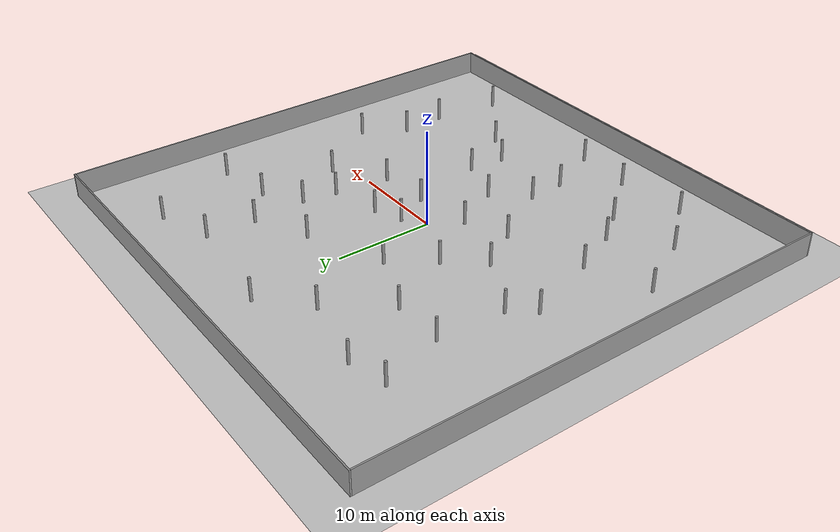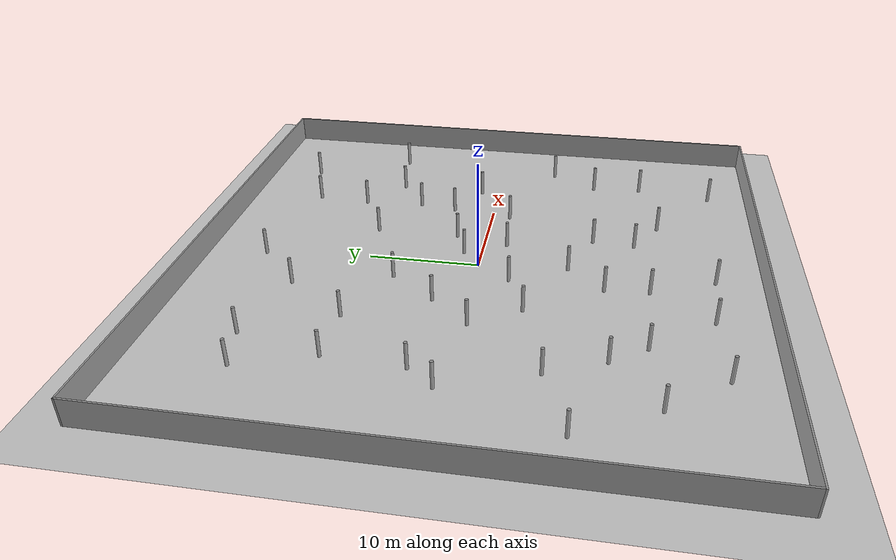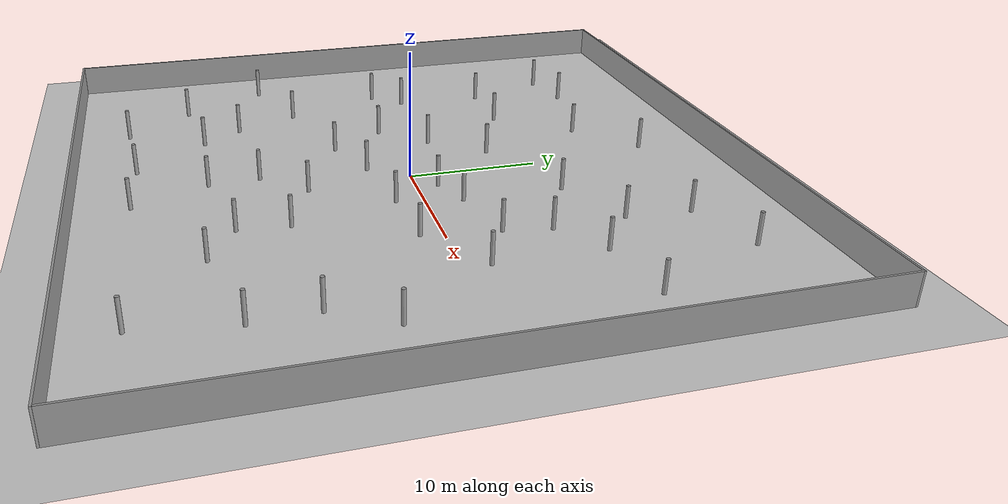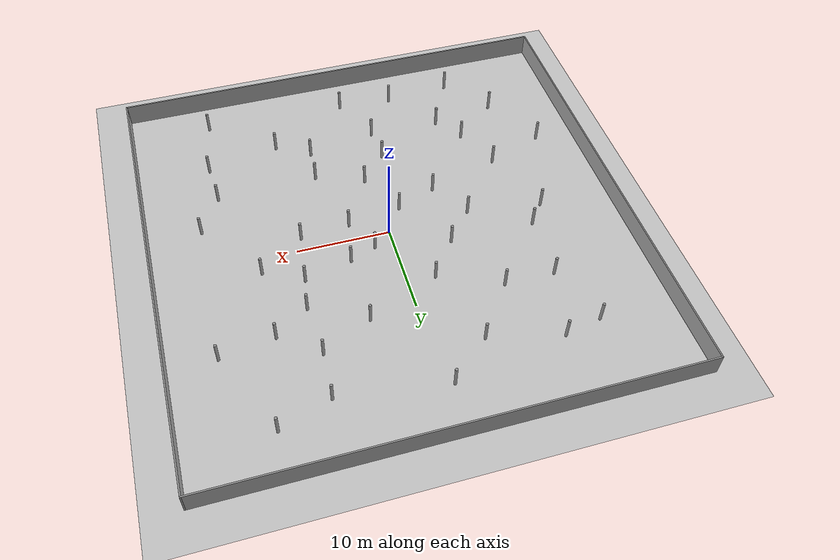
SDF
<sdf version="1.7">
 <world name="default">
  <light name="sun" type="directional">
   <pose>0 0 10 0 -0 0</pose>
   <diffuse>0.8 0.8 0.8 1</diffuse>
   <specular>0.2 0.2 0.2 1</specular>
   <attenuation>
    <range>1000</range>
    <constant>0.9</constant>
    <linear>0.01</linear>
    <quadratic>0.001</quadratic>
   </attenuation>
   <direction>-0.5 0.1 -0.9</direction>
   <spot><inner_angle>0</inner_angle><outer_angle>0</outer_angle><falloff>0</falloff></spot>
  </light>
  <model name="ground_plane">
   <static>1</static>
   <link name="link">
    <collision name="collision">
     <geometry><plane><normal>0 0 1</normal><size>100 100</size></plane></geometry>
     <surface><friction><ode><mu>100</mu><mu2>50</mu2></ode></friction></surface>
    </collision>
    <visual name="visual">
     <cast_shadows>0</cast_shadows>
     <geometry><plane><normal>0 0 1</normal><size>100 100</size></plane></geometry>
     <material>
      <script><uri>file://media/materials/scripts/gazebo.material</uri><name>Gazebo/Grey</name></script>
     </material>
    </visual>
   </link>
  </model>
  <gravity>0 0 -9.8</gravity>
  <magnetic_field>6e-06 2.3e-05 -4.2e-05</magnetic_field>
  <atmosphere type="adiabatic"/>
  <physics type="ode">
   <max_step_size>0.001</max_step_size>
   <real_time_factor>1</real_time_factor>
   <real_time_update_rate>1000</real_time_update_rate>
  </physics>
  <scene><ambient>0.4 0.4 0.4 1</ambient><background>0.7 0.7 0.7 1</background><shadows>1</shadows></scene>
  <spherical_coordinates>
   <surface_model>EARTH_WGS84</surface_model>
   <latitude_deg>0</latitude_deg>
   <longitude_deg>0</longitude_deg>
   <elevation>0</elevation>
   <heading_deg>0</heading_deg>
  </spherical_coordinates>
  <model name="fence50">
   <link name="Wall_0">
    <collision name="Wall_0_Collision">
     <geometry><box><size>50.15 0.15 2.5</size></box></geometry>
     <pose>0 0 1.25 0 -0 0</pose>
    </collision>
    <visual name="Wall_0_Visual">
     <pose>0 0 1.25 0 -0 0</pose>
     <geometry><box><size>50.15 0.15 2.5</size></box></geometry>
     <material>
      <script><uri>file://media/materials/scripts/gazebo.material</uri><name>Gazebo/Grey</name></script>
      <ambient>1 1 1 1</ambient>
     </material>
     <meta><layer>0</layer></meta>
    </visual>
    <pose>0 25 0 0 -0 3.14159</pose>
   </link>
   <link name="Wall_1">
    <collision name="Wall_1_Collision">
     <geometry><box><size>50.15 0.15 2.5</size></box></geometry>
     <pose>0 0 1.25 0 -0 0</pose>
    </collision>
    <visual name="Wall_1_Visual">
     <pose>0 0 1.25 0 -0 0</pose>
     <geometry><box><size>50.15 0.15 2.5</size></box></geometry>
     <material>
      <script><uri>file://media/materials/scripts/gazebo.material</uri><name>Gazebo/Grey</name></script>
      <ambient>1 1 1 1</ambient>
     </material>
     <meta><layer>0</layer></meta>
    </visual>
    <pose>-25 0 0 0 -0 -1.5708</pose>
   </link>
   <link name="Wall_2">
    <collision name="Wall_2_Collision">
     <geometry><box><size>50.1504 0.15 2.5</size></box></geometry>
     <pose>0 0 1.25 0 -0 0</pose>
    </collision>
    <visual name="Wall_2_Visual">
     <pose>0 0 1.25 0 -0 0</pose>
     <geometry><box><size>50.1504 0.15 2.5</size></box></geometry>
     <material>
      <script><uri>file://media/materials/scripts/gazebo.material</uri><name>Gazebo/Grey</name></script>
      <ambient>1 1 1 1</ambient>
     </material>
     <meta><layer>0</layer></meta>
    </visual>
    <pose>0 -25 0 0 -0 0</pose>
   </link>
   <link name="Wall_3">
    <collision name="Wall_3_Collision">
     <geometry><box><size>50.15 0.15 2.5</size></box></geometry>
     <pose>0 0 1.25 0 -0 0</pose>
    </collision>
    <visual name="Wall_3_Visual">
     <pose>0 0 1.25 0 -0 0</pose>
     <geometry><box><size>50.15 0.15 2.5</size></box></geometry>
     <material>
      <script><uri>file://media/materials/scripts/gazebo.material</uri><name>Gazebo/Grey</name></script>
      <ambient>1 1 1 1</ambient>
     </material>
     <meta><layer>0</layer></meta>
    </visual>
    <pose>25 0 0 0 -0 1.5708</pose>
   </link>
   <static>1</static>
  </model>
  <model name="pillar30">
   <link name="link">
    <inertial>
     <mass>1</mass>
     <inertia><ixx>0.145833</ixx><ixy>0</ixy><ixz>0</ixz><iyy>0.145833</iyy><iyz>0</iyz><izz>0.125</izz></inertia>
    </inertial>
    <kinematic>1</kinematic>
    <visual name="visual">
     <geometry><cylinder><radius>0.15</radius><length>2.5</length></cylinder></geometry>
     <material>
      <script><name>Gazebo/Grey</name><uri>file://media/materials/scripts/gazebo.material</uri></script>
      <shader type="pixel"><normal_map>__default__</normal_map></shader>
      <ambient>0.3 0.3 0.3 1</ambient>
      <diffuse>0.7 0.7 0.7 1</diffuse>
      <specular>0.01 0.01 0.01 1</specular>
      <emissive>0 0 0 1</emissive>
     </material>
    </visual>
    <collision name="collision">
     <geometry><cylinder><radius>0.15</radius><length>2.5</length></cylinder></geometry>
     <surface>
      <friction>
       <ode><mu>1</mu><mu2>1</mu2><fdir1>0 0 0</fdir1><slip1>0</slip1><slip2>0</slip2></ode>
       <torsional>
        <coefficient>1</coefficient>
        <patch_radius>0</patch_radius>
        <surface_radius>0</surface_radius>
        <use_patch_radius>1</use_patch_radius>
        <ode><slip>0</slip></ode>
       </torsional>
      </friction>
      <bounce><restitution_coefficient>0</restitution_coefficient><threshold>1e+06</threshold></bounce>
      <contact>
       <collide_without_contact>0</collide_without_contact>
       <collide_without_contact_bitmask>1</collide_without_contact_bitmask>
       <collide_bitmask>1</collide_bitmask>
       <ode>
        <soft_cfm>0</soft_cfm>
        <soft_erp>0.2</soft_erp>
        <kp>1e+13</kp>
        <kd>1</kd>
        <max_vel>0.01</max_vel>
        <min_depth>0</min_depth>
       </ode>
       <bullet>
        <split_impulse>1</split_impulse>
        <split_impulse_penetration_threshold>-0.01</split_impulse_penetration_threshold>
        <soft_cfm>0</soft_cfm>
        <soft_erp>0.2</soft_erp>
        <kp>1e+13</kp>
        <kd>1</kd>
       </bullet>
      </contact>
     </surface>
    </collision>
   </link>
   <static>0</static>
   <pose>2 1.63929 1.24999 0 0 -9e-05</pose>
  </model>
  <model name="pillar30_clone">
   <link name="link">
    <inertial>
     <mass>1</mass>
     <inertia><ixx>0.145833</ixx><ixy>0</ixy><ixz>0</ixz><iyy>0.145833</iyy><iyz>0</iyz><izz>0.125</izz></inertia>
    </inertial>
    <kinematic>1</kinematic>
    <visual name="visual">
     <geometry><cylinder><radius>0.15</radius><length>2.5</length></cylinder></geometry>
     <material>
      <script><name>Gazebo/Grey</name><uri>file://media/materials/scripts/gazebo.material</uri></script>
      <shader type="pixel"><normal_map>__default__</normal_map></shader>
      <ambient>0.3 0.3 0.3 1</ambient>
      <diffuse>0.7 0.7 0.7 1</diffuse>
      <specular>0.01 0.01 0.01 1</specular>
      <emissive>0 0 0 1</emissive>
     </material>
    </visual>
    <collision name="collision">
     <geometry><cylinder><radius>0.15</radius><length>2.5</length></cylinder></geometry>
     <surface>
      <friction>
       <ode><mu>1</mu><mu2>1</mu2><fdir1>0 0 0</fdir1><slip1>0</slip1><slip2>0</slip2></ode>
       <torsional>
        <coefficient>1</coefficient>
        <patch_radius>0</patch_radius>
        <surface_radius>0</surface_radius>
        <use_patch_radius>1</use_patch_radius>
        <ode><slip>0</slip></ode>
       </torsional>
      </friction>
      <bounce><restitution_coefficient>0</restitution_coefficient><threshold>1e+06</threshold></bounce>
      <contact>
       <collide_without_contact>0</collide_without_contact>
       <collide_without_contact_bitmask>1</collide_without_contact_bitmask>
       <collide_bitmask>1</collide_bitmask>
       <ode>
        <soft_cfm>0</soft_cfm>
        <soft_erp>0.2</soft_erp>
        <kp>1e+13</kp>
        <kd>1</kd>
        <max_vel>0.01</max_vel>
        <min_depth>0</min_depth>
       </ode>
       <bullet>
        <split_impulse>1</split_impulse>
        <split_impulse_penetration_threshold>-0.01</split_impulse_penetration_threshold>
        <soft_cfm>0</soft_cfm>
        <soft_erp>0.2</soft_erp>
        <kp>1e+13</kp>
        <kd>1</kd>
       </bullet>
      </contact>
     </surface>
    </collision>
   </link>
   <static>0</static>
   <pose>4.86662 2.77531 1.25 0 0 -8.9e-05</pose>
  </model>
  <model name="pillar30_clone_0">
   <link name="link">
    <inertial>
     <mass>1</mass>
     <inertia><ixx>0.145833</ixx><ixy>0</ixy><ixz>0</ixz><iyy>0.145833</iyy><iyz>0</iyz><izz>0.125</izz></inertia>
    </inertial>
    <kinematic>1</kinematic>
    <visual name="visual">
     <geometry><cylinder><radius>0.15</radius><length>2.5</length></cylinder></geometry>
     <material>
      <script><name>Gazebo/Grey</name><uri>file://media/materials/scripts/gazebo.material</uri></script>
      <shader type="pixel"><normal_map>__default__</normal_map></shader>
      <ambient>0.3 0.3 0.3 1</ambient>
      <diffuse>0.7 0.7 0.7 1</diffuse>
      <specular>0.01 0.01 0.01 1</specular>
      <emissive>0 0 0 1</emissive>
     </material>
    </visual>
    <collision name="collision">
     <geometry><cylinder><radius>0.15</radius><length>2.5</length></cylinder></geometry>
     <surface>
      <friction>
       <ode><mu>1</mu><mu2>1</mu2><fdir1>0 0 0</fdir1><slip1>0</slip1><slip2>0</slip2></ode>
       <torsional>
        <coefficient>1</coefficient>
        <patch_radius>0</patch_radius>
        <surface_radius>0</surface_radius>
        <use_patch_radius>1</use_patch_radius>
        <ode><slip>0</slip></ode>
       </torsional>
      </friction>
      <bounce><restitution_coefficient>0</restitution_coefficient><threshold>1e+06</threshold></bounce>
      <contact>
       <collide_without_contact>0</collide_without_contact>
       <collide_without_contact_bitmask>1</collide_without_contact_bitmask>
       <collide_bitmask>1</collide_bitmask>
       <ode>
        <soft_cfm>0</soft_cfm>
        <soft_erp>0.2</soft_erp>
        <kp>1e+13</kp>
        <kd>1</kd>
        <max_vel>0.01</max_vel>
        <min_depth>0</min_depth>
       </ode>
       <bullet>
        <split_impulse>1</split_impulse>
        <split_impulse_penetration_threshold>-0.01</split_impulse_penetration_threshold>
        <soft_cfm>0</soft_cfm>
        <soft_erp>0.2</soft_erp>
        <kp>1e+13</kp>
        <kd>1</kd>
       </bullet>
      </contact>
     </surface>
    </collision>
   </link>
   <static>0</static>
   <pose>3.88666 -2.08237 1.25 0 0 -8.9e-05</pose>
  </model>
  <model name="pillar30_clone_1">
   <link name="link">
    <inertial>
     <mass>1</mass>
     <inertia><ixx>0.145833</ixx><ixy>0</ixy><ixz>0</ixz><iyy>0.145833</iyy><iyz>0</iyz><izz>0.125</izz></inertia>
    </inertial>
    <kinematic>1</kinematic>
    <visual name="visual">
     <geometry><cylinder><radius>0.15</radius><length>2.5</length></cylinder></geometry>
     <material>
      <script><name>Gazebo/Grey</name><uri>file://media/materials/scripts/gazebo.material</uri></script>
      <shader type="pixel"><normal_map>__default__</normal_map></shader>
      <ambient>0.3 0.3 0.3 1</ambient>
      <diffuse>0.7 0.7 0.7 1</diffuse>
      <specular>0.01 0.01 0.01 1</specular>
      <emissive>0 0 0 1</emissive>
     </material>
    </visual>
    <collision name="collision">
     <geometry><cylinder><radius>0.15</radius><length>2.5</length></cylinder></geometry>
     <surface>
      <friction>
       <ode><mu>1</mu><mu2>1</mu2><fdir1>0 0 0</fdir1><slip1>0</slip1><slip2>0</slip2></ode>
       <torsional>
        <coefficient>1</coefficient>
        <patch_radius>0</patch_radius>
        <surface_radius>0</surface_radius>
        <use_patch_radius>1</use_patch_radius>
        <ode><slip>0</slip></ode>
       </torsional>
      </friction>
      <bounce><restitution_coefficient>0</restitution_coefficient><threshold>1e+06</threshold></bounce>
      <contact>
       <collide_without_contact>0</collide_without_contact>
       <collide_without_contact_bitmask>1</collide_without_contact_bitmask>
       <collide_bitmask>1</collide_bitmask>
       <ode>
        <soft_cfm>0</soft_cfm>
        <soft_erp>0.2</soft_erp>
        <kp>1e+13</kp>
        <kd>1</kd>
        <max_vel>0.01</max_vel>
        <min_depth>0</min_depth>
       </ode>
       <bullet>
        <split_impulse>1</split_impulse>
        <split_impulse_penetration_threshold>-0.01</split_impulse_penetration_threshold>
        <soft_cfm>0</soft_cfm>
        <soft_erp>0.2</soft_erp>
        <kp>1e+13</kp>
        <kd>1</kd>
       </bullet>
      </contact>
     </surface>
    </collision>
   </link>
   <static>0</static>
   <pose>9.22545 -1.66663 1.25 0 0 -8.9e-05</pose>
  </model>
  <model name="pillar30_clone_2">
   <link name="link">
    <inertial>
     <mass>1</mass>
     <inertia><ixx>0.145833</ixx><ixy>0</ixy><ixz>0</ixz><iyy>0.145833</iyy><iyz>0</iyz><izz>0.125</izz></inertia>
    </inertial>
    <kinematic>1</kinematic>
    <visual name="visual">
     <geometry><cylinder><radius>0.15</radius><length>2.5</length></cylinder></geometry>
     <material>
      <script><name>Gazebo/Grey</name><uri>file://media/materials/scripts/gazebo.material</uri></script>
      <shader type="pixel"><normal_map>__default__</normal_map></shader>
      <ambient>0.3 0.3 0.3 1</ambient>
      <diffuse>0.7 0.7 0.7 1</diffuse>
      <specular>0.01 0.01 0.01 1</specular>
      <emissive>0 0 0 1</emissive>
     </material>
    </visual>
    <collision name="collision">
     <geometry><cylinder><radius>0.15</radius><length>2.5</length></cylinder></geometry>
     <surface>
      <friction>
       <ode><mu>1</mu><mu2>1</mu2><fdir1>0 0 0</fdir1><slip1>0</slip1><slip2>0</slip2></ode>
       <torsional>
        <coefficient>1</coefficient>
        <patch_radius>0</patch_radius>
        <surface_radius>0</surface_radius>
        <use_patch_radius>1</use_patch_radius>
        <ode><slip>0</slip></ode>
       </torsional>
      </friction>
      <bounce><restitution_coefficient>0</restitution_coefficient><threshold>1e+06</threshold></bounce>
      <contact>
       <collide_without_contact>0</collide_without_contact>
       <collide_without_contact_bitmask>1</collide_without_contact_bitmask>
       <collide_bitmask>1</collide_bitmask>
       <ode>
        <soft_cfm>0</soft_cfm>
        <soft_erp>0.2</soft_erp>
        <kp>1e+13</kp>
        <kd>1</kd>
        <max_vel>0.01</max_vel>
        <min_depth>0</min_depth>
       </ode>
       <bullet>
        <split_impulse>1</split_impulse>
        <split_impulse_penetration_threshold>-0.01</split_impulse_penetration_threshold>
        <soft_cfm>0</soft_cfm>
        <soft_erp>0.2</soft_erp>
        <kp>1e+13</kp>
        <kd>1</kd>
       </bullet>
      </contact>
     </surface>
    </collision>
   </link>
   <static>0</static>
   <pose>14.0902 1.8625 1.25 0 0 -8.9e-05</pose>
  </model>
  <model name="pillar30_clone_3">
   <link name="link">
    <inertial>
     <mass>1</mass>
     <inertia><ixx>0.145833</ixx><ixy>0</ixy><ixz>0</ixz><iyy>0.145833</iyy><iyz>0</iyz><izz>0.125</izz></inertia>
    </inertial>
    <kinematic>1</kinematic>
    <visual name="visual">
     <geometry><cylinder><radius>0.15</radius><length>2.5</length></cylinder></geometry>
     <material>
      <script><name>Gazebo/Grey</name><uri>file://media/materials/scripts/gazebo.material</uri></script>
      <shader type="pixel"><normal_map>__default__</normal_map></shader>
      <ambient>0.3 0.3 0.3 1</ambient>
      <diffuse>0.7 0.7 0.7 1</diffuse>
      <specular>0.01 0.01 0.01 1</specular>
      <emissive>0 0 0 1</emissive>
     </material>
    </visual>
    <collision name="collision">
     <geometry><cylinder><radius>0.15</radius><length>2.5</length></cylinder></geometry>
     <surface>
      <friction>
       <ode><mu>1</mu><mu2>1</mu2><fdir1>0 0 0</fdir1><slip1>0</slip1><slip2>0</slip2></ode>
       <torsional>
        <coefficient>1</coefficient>
        <patch_radius>0</patch_radius>
        <surface_radius>0</surface_radius>
        <use_patch_radius>1</use_patch_radius>
        <ode><slip>0</slip></ode>
       </torsional>
      </friction>
      <bounce><restitution_coefficient>0</restitution_coefficient><threshold>1e+06</threshold></bounce>
      <contact>
       <collide_without_contact>0</collide_without_contact>
       <collide_without_contact_bitmask>1</collide_without_contact_bitmask>
       <collide_bitmask>1</collide_bitmask>
       <ode>
        <soft_cfm>0</soft_cfm>
        <soft_erp>0.2</soft_erp>
        <kp>1e+13</kp>
        <kd>1</kd>
        <max_vel>0.01</max_vel>
        <min_depth>0</min_depth>
       </ode>
       <bullet>
        <split_impulse>1</split_impulse>
        <split_impulse_penetration_threshold>-0.01</split_impulse_penetration_threshold>
        <soft_cfm>0</soft_cfm>
        <soft_erp>0.2</soft_erp>
        <kp>1e+13</kp>
        <kd>1</kd>
       </bullet>
      </contact>
     </surface>
    </collision>
   </link>
   <static>0</static>
   <pose>14.2126 10.0495 1.25 0 0 -8.9e-05</pose>
  </model>
  <model name="pillar30_clone_4">
   <link name="link">
    <inertial>
     <mass>1</mass>
     <inertia><ixx>0.145833</ixx><ixy>0</ixy><ixz>0</ixz><iyy>0.145833</iyy><iyz>0</iyz><izz>0.125</izz></inertia>
    </inertial>
    <kinematic>1</kinematic>
    <visual name="visual">
     <geometry><cylinder><radius>0.15</radius><length>2.5</length></cylinder></geometry>
     <material>
      <script><name>Gazebo/Grey</name><uri>file://media/materials/scripts/gazebo.material</uri></script>
      <shader type="pixel"><normal_map>__default__</normal_map></shader>
      <ambient>0.3 0.3 0.3 1</ambient>
      <diffuse>0.7 0.7 0.7 1</diffuse>
      <specular>0.01 0.01 0.01 1</specular>
      <emissive>0 0 0 1</emissive>
     </material>
    </visual>
    <collision name="collision">
     <geometry><cylinder><radius>0.15</radius><length>2.5</length></cylinder></geometry>
     <surface>
      <friction>
       <ode><mu>1</mu><mu2>1</mu2><fdir1>0 0 0</fdir1><slip1>0</slip1><slip2>0</slip2></ode>
       <torsional>
        <coefficient>1</coefficient>
        <patch_radius>0</patch_radius>
        <surface_radius>0</surface_radius>
        <use_patch_radius>1</use_patch_radius>
        <ode><slip>0</slip></ode>
       </torsional>
      </friction>
      <bounce><restitution_coefficient>0</restitution_coefficient><threshold>1e+06</threshold></bounce>
      <contact>
       <collide_without_contact>0</collide_without_contact>
       <collide_without_contact_bitmask>1</collide_without_contact_bitmask>
       <collide_bitmask>1</collide_bitmask>
       <ode>
        <soft_cfm>0</soft_cfm>
        <soft_erp>0.2</soft_erp>
        <kp>1e+13</kp>
        <kd>1</kd>
        <max_vel>0.01</max_vel>
        <min_depth>0</min_depth>
       </ode>
       <bullet>
        <split_impulse>1</split_impulse>
        <split_impulse_penetration_threshold>-0.01</split_impulse_penetration_threshold>
        <soft_cfm>0</soft_cfm>
        <soft_erp>0.2</soft_erp>
        <kp>1e+13</kp>
        <kd>1</kd>
       </bullet>
      </contact>
     </surface>
    </collision>
   </link>
   <static>0</static>
   <pose>10.2181 13.111 1.25 0 0 -8.9e-05</pose>
  </model>
  <model name="pillar30_clone_5">
   <link name="link">
    <inertial>
     <mass>1</mass>
     <inertia><ixx>0.145833</ixx><ixy>0</ixy><ixz>0</ixz><iyy>0.145833</iyy><iyz>0</iyz><izz>0.125</izz></inertia>
    </inertial>
    <kinematic>1</kinematic>
    <visual name="visual">
     <geometry><cylinder><radius>0.15</radius><length>2.5</length></cylinder></geometry>
     <material>
      <script><name>Gazebo/Grey</name><uri>file://media/materials/scripts/gazebo.material</uri></script>
      <shader type="pixel"><normal_map>__default__</normal_map></shader>
      <ambient>0.3 0.3 0.3 1</ambient>
      <diffuse>0.7 0.7 0.7 1</diffuse>
      <specular>0.01 0.01 0.01 1</specular>
      <emissive>0 0 0 1</emissive>
     </material>
    </visual>
    <collision name="collision">
     <geometry><cylinder><radius>0.15</radius><length>2.5</length></cylinder></geometry>
     <surface>
      <friction>
       <ode><mu>1</mu><mu2>1</mu2><fdir1>0 0 0</fdir1><slip1>0</slip1><slip2>0</slip2></ode>
       <torsional>
        <coefficient>1</coefficient>
        <patch_radius>0</patch_radius>
        <surface_radius>0</surface_radius>
        <use_patch_radius>1</use_patch_radius>
        <ode><slip>0</slip></ode>
       </torsional>
      </friction>
      <bounce><restitution_coefficient>0</restitution_coefficient><threshold>1e+06</threshold></bounce>
      <contact>
       <collide_without_contact>0</collide_without_contact>
       <collide_without_contact_bitmask>1</collide_without_contact_bitmask>
       <collide_bitmask>1</collide_bitmask>
       <ode>
        <soft_cfm>0</soft_cfm>
        <soft_erp>0.2</soft_erp>
        <kp>1e+13</kp>
        <kd>1</kd>
        <max_vel>0.01</max_vel>
        <min_depth>0</min_depth>
       </ode>
       <bullet>
        <split_impulse>1</split_impulse>
        <split_impulse_penetration_threshold>-0.01</split_impulse_penetration_threshold>
        <soft_cfm>0</soft_cfm>
        <soft_erp>0.2</soft_erp>
        <kp>1e+13</kp>
        <kd>1</kd>
       </bullet>
      </contact>
     </surface>
    </collision>
   </link>
   <static>0</static>
   <pose>4.85597 10.4651 1.25 0 0 -8.9e-05</pose>
  </model>
  <model name="pillar30_clone_6">
   <link name="link">
    <inertial>
     <mass>1</mass>
     <inertia><ixx>0.145833</ixx><ixy>0</ixy><ixz>0</ixz><iyy>0.145833</iyy><iyz>0</iyz><izz>0.125</izz></inertia>
    </inertial>
    <kinematic>1</kinematic>
    <visual name="visual">
     <geometry><cylinder><radius>0.15</radius><length>2.5</length></cylinder></geometry>
     <material>
      <script><name>Gazebo/Grey</name><uri>file://media/materials/scripts/gazebo.material</uri></script>
      <shader type="pixel"><normal_map>__default__</normal_map></shader>
      <ambient>0.3 0.3 0.3 1</ambient>
      <diffuse>0.7 0.7 0.7 1</diffuse>
      <specular>0.01 0.01 0.01 1</specular>
      <emissive>0 0 0 1</emissive>
     </material>
    </visual>
    <collision name="collision">
     <geometry><cylinder><radius>0.15</radius><length>2.5</length></cylinder></geometry>
     <surface>
      <friction>
       <ode><mu>1</mu><mu2>1</mu2><fdir1>0 0 0</fdir1><slip1>0</slip1><slip2>0</slip2></ode>
       <torsional>
        <coefficient>1</coefficient>
        <patch_radius>0</patch_radius>
        <surface_radius>0</surface_radius>
        <use_patch_radius>1</use_patch_radius>
        <ode><slip>0</slip></ode>
       </torsional>
      </friction>
      <bounce><restitution_coefficient>0</restitution_coefficient><threshold>1e+06</threshold></bounce>
      <contact>
       <collide_without_contact>0</collide_without_contact>
       <collide_without_contact_bitmask>1</collide_without_contact_bitmask>
       <collide_bitmask>1</collide_bitmask>
       <ode>
        <soft_cfm>0</soft_cfm>
        <soft_erp>0.2</soft_erp>
        <kp>1e+13</kp>
        <kd>1</kd>
        <max_vel>0.01</max_vel>
        <min_depth>0</min_depth>
       </ode>
       <bullet>
        <split_impulse>1</split_impulse>
        <split_impulse_penetration_threshold>-0.01</split_impulse_penetration_threshold>
        <soft_cfm>0</soft_cfm>
        <soft_erp>0.2</soft_erp>
        <kp>1e+13</kp>
        <kd>1</kd>
       </bullet>
      </contact>
     </surface>
    </collision>
   </link>
   <static>0</static>
   <pose>10.5745 7.50783 1.25 0 0 -8.9e-05</pose>
  </model>
  <model name="pillar30_clone_7">
   <link name="link">
    <inertial>
     <mass>1</mass>
     <inertia><ixx>0.145833</ixx><ixy>0</ixy><ixz>0</ixz><iyy>0.145833</iyy><iyz>0</iyz><izz>0.125</izz></inertia>
    </inertial>
    <kinematic>1</kinematic>
    <visual name="visual">
     <geometry><cylinder><radius>0.15</radius><length>2.5</length></cylinder></geometry>
     <material>
      <script><name>Gazebo/Grey</name><uri>file://media/materials/scripts/gazebo.material</uri></script>
      <shader type="pixel"><normal_map>__default__</normal_map></shader>
      <ambient>0.3 0.3 0.3 1</ambient>
      <diffuse>0.7 0.7 0.7 1</diffuse>
      <specular>0.01 0.01 0.01 1</specular>
      <emissive>0 0 0 1</emissive>
     </material>
    </visual>
    <collision name="collision">
     <geometry><cylinder><radius>0.15</radius><length>2.5</length></cylinder></geometry>
     <surface>
      <friction>
       <ode><mu>1</mu><mu2>1</mu2><fdir1>0 0 0</fdir1><slip1>0</slip1><slip2>0</slip2></ode>
       <torsional>
        <coefficient>1</coefficient>
        <patch_radius>0</patch_radius>
        <surface_radius>0</surface_radius>
        <use_patch_radius>1</use_patch_radius>
        <ode><slip>0</slip></ode>
       </torsional>
      </friction>
      <bounce><restitution_coefficient>0</restitution_coefficient><threshold>1e+06</threshold></bounce>
      <contact>
       <collide_without_contact>0</collide_without_contact>
       <collide_without_contact_bitmask>1</collide_without_contact_bitmask>
       <collide_bitmask>1</collide_bitmask>
       <ode>
        <soft_cfm>0</soft_cfm>
        <soft_erp>0.2</soft_erp>
        <kp>1e+13</kp>
        <kd>1</kd>
        <max_vel>0.01</max_vel>
        <min_depth>0</min_depth>
       </ode>
       <bullet>
        <split_impulse>1</split_impulse>
        <split_impulse_penetration_threshold>-0.01</split_impulse_penetration_threshold>
        <soft_cfm>0</soft_cfm>
        <soft_erp>0.2</soft_erp>
        <kp>1e+13</kp>
        <kd>1</kd>
       </bullet>
      </contact>
     </surface>
    </collision>
   </link>
   <static>0</static>
   <pose>10 4 1.25 0 0 -8.9e-05</pose>
  </model>
  <model name="pillar30_clone_8">
   <link name="link">
    <inertial>
     <mass>1</mass>
     <inertia><ixx>0.145833</ixx><ixy>0</ixy><ixz>0</ixz><iyy>0.145833</iyy><iyz>0</iyz><izz>0.125</izz></inertia>
    </inertial>
    <kinematic>1</kinematic>
    <visual name="visual">
     <geometry><cylinder><radius>0.15</radius><length>2.5</length></cylinder></geometry>
     <material>
      <script><name>Gazebo/Grey</name><uri>file://media/materials/scripts/gazebo.material</uri></script>
      <shader type="pixel"><normal_map>__default__</normal_map></shader>
      <ambient>0.3 0.3 0.3 1</ambient>
      <diffuse>0.7 0.7 0.7 1</diffuse>
      <specular>0.01 0.01 0.01 1</specular>
      <emissive>0 0 0 1</emissive>
     </material>
    </visual>
    <collision name="collision">
     <geometry><cylinder><radius>0.15</radius><length>2.5</length></cylinder></geometry>
     <surface>
      <friction>
       <ode><mu>1</mu><mu2>1</mu2><fdir1>0 0 0</fdir1><slip1>0</slip1><slip2>0</slip2></ode>
       <torsional>
        <coefficient>1</coefficient>
        <patch_radius>0</patch_radius>
        <surface_radius>0</surface_radius>
        <use_patch_radius>1</use_patch_radius>
        <ode><slip>0</slip></ode>
       </torsional>
      </friction>
      <bounce><restitution_coefficient>0</restitution_coefficient><threshold>1e+06</threshold></bounce>
      <contact>
       <collide_without_contact>0</collide_without_contact>
       <collide_without_contact_bitmask>1</collide_without_contact_bitmask>
       <collide_bitmask>1</collide_bitmask>
       <ode>
        <soft_cfm>0</soft_cfm>
        <soft_erp>0.2</soft_erp>
        <kp>1e+13</kp>
        <kd>1</kd>
        <max_vel>0.01</max_vel>
        <min_depth>0</min_depth>
       </ode>
       <bullet>
        <split_impulse>1</split_impulse>
        <split_impulse_penetration_threshold>-0.01</split_impulse_penetration_threshold>
        <soft_cfm>0</soft_cfm>
        <soft_erp>0.2</soft_erp>
        <kp>1e+13</kp>
        <kd>1</kd>
       </bullet>
      </contact>
     </surface>
    </collision>
   </link>
   <static>0</static>
   <pose>10 4 1.25 0 0 -8.9e-05</pose>
  </model>
  <model name="pillar30_clone_9">
   <link name="link">
    <inertial>
     <mass>1</mass>
     <inertia><ixx>0.145833</ixx><ixy>0</ixy><ixz>0</ixz><iyy>0.145833</iyy><iyz>0</iyz><izz>0.125</izz></inertia>
    </inertial>
    <kinematic>1</kinematic>
    <visual name="visual">
     <geometry><cylinder><radius>0.15</radius><length>2.5</length></cylinder></geometry>
     <material>
      <script><name>Gazebo/Grey</name><uri>file://media/materials/scripts/gazebo.material</uri></script>
      <shader type="pixel"><normal_map>__default__</normal_map></shader>
      <ambient>0.3 0.3 0.3 1</ambient>
      <diffuse>0.7 0.7 0.7 1</diffuse>
      <specular>0.01 0.01 0.01 1</specular>
      <emissive>0 0 0 1</emissive>
     </material>
    </visual>
    <collision name="collision">
     <geometry><cylinder><radius>0.15</radius><length>2.5</length></cylinder></geometry>
     <surface>
      <friction>
       <ode><mu>1</mu><mu2>1</mu2><fdir1>0 0 0</fdir1><slip1>0</slip1><slip2>0</slip2></ode>
       <torsional>
        <coefficient>1</coefficient>
        <patch_radius>0</patch_radius>
        <surface_radius>0</surface_radius>
        <use_patch_radius>1</use_patch_radius>
        <ode><slip>0</slip></ode>
       </torsional>
      </friction>
      <bounce><restitution_coefficient>0</restitution_coefficient><threshold>1e+06</threshold></bounce>
      <contact>
       <collide_without_contact>0</collide_without_contact>
       <collide_without_contact_bitmask>1</collide_without_contact_bitmask>
       <collide_bitmask>1</collide_bitmask>
       <ode>
        <soft_cfm>0</soft_cfm>
        <soft_erp>0.2</soft_erp>
        <kp>1e+13</kp>
        <kd>1</kd>
        <max_vel>0.01</max_vel>
        <min_depth>0</min_depth>
       </ode>
       <bullet>
        <split_impulse>1</split_impulse>
        <split_impulse_penetration_threshold>-0.01</split_impulse_penetration_threshold>
        <soft_cfm>0</soft_cfm>
        <soft_erp>0.2</soft_erp>
        <kp>1e+13</kp>
        <kd>1</kd>
       </bullet>
      </contact>
     </surface>
    </collision>
   </link>
   <static>0</static>
   <pose>-2.94396 7.10359 1.25 0 0 -8.9e-05</pose>
  </model>
  <model name="pillar30_clone_10">
   <link name="link">
    <inertial>
     <mass>1</mass>
     <inertia><ixx>0.145833</ixx><ixy>0</ixy><ixz>0</ixz><iyy>0.145833</iyy><iyz>0</iyz><izz>0.125</izz></inertia>
    </inertial>
    <kinematic>1</kinematic>
    <visual name="visual">
     <geometry><cylinder><radius>0.15</radius><length>2.5</length></cylinder></geometry>
     <material>
      <script><name>Gazebo/Grey</name><uri>file://media/materials/scripts/gazebo.material</uri></script>
      <shader type="pixel"><normal_map>__default__</normal_map></shader>
      <ambient>0.3 0.3 0.3 1</ambient>
      <diffuse>0.7 0.7 0.7 1</diffuse>
      <specular>0.01 0.01 0.01 1</specular>
      <emissive>0 0 0 1</emissive>
     </material>
    </visual>
    <collision name="collision">
     <geometry><cylinder><radius>0.15</radius><length>2.5</length></cylinder></geometry>
     <surface>
      <friction>
       <ode><mu>1</mu><mu2>1</mu2><fdir1>0 0 0</fdir1><slip1>0</slip1><slip2>0</slip2></ode>
       <torsional>
        <coefficient>1</coefficient>
        <patch_radius>0</patch_radius>
        <surface_radius>0</surface_radius>
        <use_patch_radius>1</use_patch_radius>
        <ode><slip>0</slip></ode>
       </torsional>
      </friction>
      <bounce><restitution_coefficient>0</restitution_coefficient><threshold>1e+06</threshold></bounce>
      <contact>
       <collide_without_contact>0</collide_without_contact>
       <collide_without_contact_bitmask>1</collide_without_contact_bitmask>
       <collide_bitmask>1</collide_bitmask>
       <ode>
        <soft_cfm>0</soft_cfm>
        <soft_erp>0.2</soft_erp>
        <kp>1e+13</kp>
        <kd>1</kd>
        <max_vel>0.01</max_vel>
        <min_depth>0</min_depth>
       </ode>
       <bullet>
        <split_impulse>1</split_impulse>
        <split_impulse_penetration_threshold>-0.01</split_impulse_penetration_threshold>
        <soft_cfm>0</soft_cfm>
        <soft_erp>0.2</soft_erp>
        <kp>1e+13</kp>
        <kd>1</kd>
       </bullet>
      </contact>
     </surface>
    </collision>
   </link>
   <static>0</static>
   <pose>-6 3 1.25 0 0 -8.9e-05</pose>
  </model>
  <model name="pillar30_clone_11">
   <link name="link">
    <inertial>
     <mass>1</mass>
     <inertia><ixx>0.145833</ixx><ixy>0</ixy><ixz>0</ixz><iyy>0.145833</iyy><iyz>0</iyz><izz>0.125</izz></inertia>
    </inertial>
    <kinematic>1</kinematic>
    <visual name="visual">
     <geometry><cylinder><radius>0.15</radius><length>2.5</length></cylinder></geometry>
     <material>
      <script><name>Gazebo/Grey</name><uri>file://media/materials/scripts/gazebo.material</uri></script>
      <shader type="pixel"><normal_map>__default__</normal_map></shader>
      <ambient>0.3 0.3 0.3 1</ambient>
      <diffuse>0.7 0.7 0.7 1</diffuse>
      <specular>0.01 0.01 0.01 1</specular>
      <emissive>0 0 0 1</emissive>
     </material>
    </visual>
    <collision name="collision">
     <geometry><cylinder><radius>0.15</radius><length>2.5</length></cylinder></geometry>
     <surface>
      <friction>
       <ode><mu>1</mu><mu2>1</mu2><fdir1>0 0 0</fdir1><slip1>0</slip1><slip2>0</slip2></ode>
       <torsional>
        <coefficient>1</coefficient>
        <patch_radius>0</patch_radius>
        <surface_radius>0</surface_radius>
        <use_patch_radius>1</use_patch_radius>
        <ode><slip>0</slip></ode>
       </torsional>
      </friction>
      <bounce><restitution_coefficient>0</restitution_coefficient><threshold>1e+06</threshold></bounce>
      <contact>
       <collide_without_contact>0</collide_without_contact>
       <collide_without_contact_bitmask>1</collide_without_contact_bitmask>
       <collide_bitmask>1</collide_bitmask>
       <ode>
        <soft_cfm>0</soft_cfm>
        <soft_erp>0.2</soft_erp>
        <kp>1e+13</kp>
        <kd>1</kd>
        <max_vel>0.01</max_vel>
        <min_depth>0</min_depth>
       </ode>
       <bullet>
        <split_impulse>1</split_impulse>
        <split_impulse_penetration_threshold>-0.01</split_impulse_penetration_threshold>
        <soft_cfm>0</soft_cfm>
        <soft_erp>0.2</soft_erp>
        <kp>1e+13</kp>
        <kd>1</kd>
       </bullet>
      </contact>
     </surface>
    </collision>
   </link>
   <static>0</static>
   <pose>-6.35506 -4.74154 1.25 0 0 -8.9e-05</pose>
  </model>
  <model name="pillar30_clone_12">
   <link name="link">
    <inertial>
     <mass>1</mass>
     <inertia><ixx>0.145833</ixx><ixy>0</ixy><ixz>0</ixz><iyy>0.145833</iyy><iyz>0</iyz><izz>0.125</izz></inertia>
    </inertial>
    <kinematic>1</kinematic>
    <visual name="visual">
     <geometry><cylinder><radius>0.15</radius><length>2.5</length></cylinder></geometry>
     <material>
      <script><name>Gazebo/Grey</name><uri>file://media/materials/scripts/gazebo.material</uri></script>
      <shader type="pixel"><normal_map>__default__</normal_map></shader>
      <ambient>0.3 0.3 0.3 1</ambient>
      <diffuse>0.7 0.7 0.7 1</diffuse>
      <specular>0.01 0.01 0.01 1</specular>
      <emissive>0 0 0 1</emissive>
     </material>
    </visual>
    <collision name="collision">
     <geometry><cylinder><radius>0.15</radius><length>2.5</length></cylinder></geometry>
     <surface>
      <friction>
       <ode><mu>1</mu><mu2>1</mu2><fdir1>0 0 0</fdir1><slip1>0</slip1><slip2>0</slip2></ode>
       <torsional>
        <coefficient>1</coefficient>
        <patch_radius>0</patch_radius>
        <surface_radius>0</surface_radius>
        <use_patch_radius>1</use_patch_radius>
        <ode><slip>0</slip></ode>
       </torsional>
      </friction>
      <bounce><restitution_coefficient>0</restitution_coefficient><threshold>1e+06</threshold></bounce>
      <contact>
       <collide_without_contact>0</collide_without_contact>
       <collide_without_contact_bitmask>1</collide_without_contact_bitmask>
       <collide_bitmask>1</collide_bitmask>
       <ode>
        <soft_cfm>0</soft_cfm>
        <soft_erp>0.2</soft_erp>
        <kp>1e+13</kp>
        <kd>1</kd>
        <max_vel>0.01</max_vel>
        <min_depth>0</min_depth>
       </ode>
       <bullet>
        <split_impulse>1</split_impulse>
        <split_impulse_penetration_threshold>-0.01</split_impulse_penetration_threshold>
        <soft_cfm>0</soft_cfm>
        <soft_erp>0.2</soft_erp>
        <kp>1e+13</kp>
        <kd>1</kd>
       </bullet>
      </contact>
     </surface>
    </collision>
   </link>
   <static>0</static>
   <pose>-14.8322 9.95336 1.25 0 0 -8.9e-05</pose>
  </model>
  <model name="pillar30_clone_13">
   <link name="link">
    <inertial>
     <mass>1</mass>
     <inertia><ixx>0.145833</ixx><ixy>0</ixy><ixz>0</ixz><iyy>0.145833</iyy><iyz>0</iyz><izz>0.125</izz></inertia>
    </inertial>
    <kinematic>1</kinematic>
    <visual name="visual">
     <geometry><cylinder><radius>0.15</radius><length>2.5</length></cylinder></geometry>
     <material>
      <script><name>Gazebo/Grey</name><uri>file://media/materials/scripts/gazebo.material</uri></script>
      <shader type="pixel"><normal_map>__default__</normal_map></shader>
      <ambient>0.3 0.3 0.3 1</ambient>
      <diffuse>0.7 0.7 0.7 1</diffuse>
      <specular>0.01 0.01 0.01 1</specular>
      <emissive>0 0 0 1</emissive>
     </material>
    </visual>
    <collision name="collision">
     <geometry><cylinder><radius>0.15</radius><length>2.5</length></cylinder></geometry>
     <surface>
      <friction>
       <ode><mu>1</mu><mu2>1</mu2><fdir1>0 0 0</fdir1><slip1>0</slip1><slip2>0</slip2></ode>
       <torsional>
        <coefficient>1</coefficient>
        <patch_radius>0</patch_radius>
        <surface_radius>0</surface_radius>
        <use_patch_radius>1</use_patch_radius>
        <ode><slip>0</slip></ode>
       </torsional>
      </friction>
      <bounce><restitution_coefficient>0</restitution_coefficient><threshold>1e+06</threshold></bounce>
      <contact>
       <collide_without_contact>0</collide_without_contact>
       <collide_without_contact_bitmask>1</collide_without_contact_bitmask>
       <collide_bitmask>1</collide_bitmask>
       <ode>
        <soft_cfm>0</soft_cfm>
        <soft_erp>0.2</soft_erp>
        <kp>1e+13</kp>
        <kd>1</kd>
        <max_vel>0.01</max_vel>
        <min_depth>0</min_depth>
       </ode>
       <bullet>
        <split_impulse>1</split_impulse>
        <split_impulse_penetration_threshold>-0.01</split_impulse_penetration_threshold>
        <soft_cfm>0</soft_cfm>
        <soft_erp>0.2</soft_erp>
        <kp>1e+13</kp>
        <kd>1</kd>
       </bullet>
      </contact>
     </surface>
    </collision>
   </link>
   <static>0</static>
   <pose>-17 16.4927 1.25 0 0 -8.9e-05</pose>
  </model>
  <model name="pillar30_clone_14">
   <link name="link">
    <inertial>
     <mass>1</mass>
     <inertia><ixx>0.145833</ixx><ixy>0</ixy><ixz>0</ixz><iyy>0.145833</iyy><iyz>0</iyz><izz>0.125</izz></inertia>
    </inertial>
    <kinematic>1</kinematic>
    <visual name="visual">
     <geometry><cylinder><radius>0.15</radius><length>2.5</length></cylinder></geometry>
     <material>
      <script><name>Gazebo/Grey</name><uri>file://media/materials/scripts/gazebo.material</uri></script>
      <shader type="pixel"><normal_map>__default__</normal_map></shader>
      <ambient>0.3 0.3 0.3 1</ambient>
      <diffuse>0.7 0.7 0.7 1</diffuse>
      <specular>0.01 0.01 0.01 1</specular>
      <emissive>0 0 0 1</emissive>
     </material>
    </visual>
    <collision name="collision">
     <geometry><cylinder><radius>0.15</radius><length>2.5</length></cylinder></geometry>
     <surface>
      <friction>
       <ode><mu>1</mu><mu2>1</mu2><fdir1>0 0 0</fdir1><slip1>0</slip1><slip2>0</slip2></ode>
       <torsional>
        <coefficient>1</coefficient>
        <patch_radius>0</patch_radius>
        <surface_radius>0</surface_radius>
        <use_patch_radius>1</use_patch_radius>
        <ode><slip>0</slip></ode>
       </torsional>
      </friction>
      <bounce><restitution_coefficient>0</restitution_coefficient><threshold>1e+06</threshold></bounce>
      <contact>
       <collide_without_contact>0</collide_without_contact>
       <collide_without_contact_bitmask>1</collide_without_contact_bitmask>
       <collide_bitmask>1</collide_bitmask>
       <ode>
        <soft_cfm>0</soft_cfm>
        <soft_erp>0.2</soft_erp>
        <kp>1e+13</kp>
        <kd>1</kd>
        <max_vel>0.01</max_vel>
        <min_depth>0</min_depth>
       </ode>
       <bullet>
        <split_impulse>1</split_impulse>
        <split_impulse_penetration_threshold>-0.01</split_impulse_penetration_threshold>
        <soft_cfm>0</soft_cfm>
        <soft_erp>0.2</soft_erp>
        <kp>1e+13</kp>
        <kd>1</kd>
       </bullet>
      </contact>
     </surface>
    </collision>
   </link>
   <static>0</static>
   <pose>-13 17.401 1.25 0 0 -8.9e-05</pose>
  </model>
  <model name="pillar30_clone_15">
   <link name="link">
    <inertial>
     <mass>1</mass>
     <inertia><ixx>0.145833</ixx><ixy>0</ixy><ixz>0</ixz><iyy>0.145833</iyy><iyz>0</iyz><izz>0.125</izz></inertia>
    </inertial>
    <kinematic>1</kinematic>
    <visual name="visual">
     <geometry><cylinder><radius>0.15</radius><length>2.5</length></cylinder></geometry>
     <material>
      <script><name>Gazebo/Grey</name><uri>file://media/materials/scripts/gazebo.material</uri></script>
      <shader type="pixel"><normal_map>__default__</normal_map></shader>
      <ambient>0.3 0.3 0.3 1</ambient>
      <diffuse>0.7 0.7 0.7 1</diffuse>
      <specular>0.01 0.01 0.01 1</specular>
      <emissive>0 0 0 1</emissive>
     </material>
    </visual>
    <collision name="collision">
     <geometry><cylinder><radius>0.15</radius><length>2.5</length></cylinder></geometry>
     <surface>
      <friction>
       <ode><mu>1</mu><mu2>1</mu2><fdir1>0 0 0</fdir1><slip1>0</slip1><slip2>0</slip2></ode>
       <torsional>
        <coefficient>1</coefficient>
        <patch_radius>0</patch_radius>
        <surface_radius>0</surface_radius>
        <use_patch_radius>1</use_patch_radius>
        <ode><slip>0</slip></ode>
       </torsional>
      </friction>
      <bounce><restitution_coefficient>0</restitution_coefficient><threshold>1e+06</threshold></bounce>
      <contact>
       <collide_without_contact>0</collide_without_contact>
       <collide_without_contact_bitmask>1</collide_without_contact_bitmask>
       <collide_bitmask>1</collide_bitmask>
       <ode>
        <soft_cfm>0</soft_cfm>
        <soft_erp>0.2</soft_erp>
        <kp>1e+13</kp>
        <kd>1</kd>
        <max_vel>0.01</max_vel>
        <min_depth>0</min_depth>
       </ode>
       <bullet>
        <split_impulse>1</split_impulse>
        <split_impulse_penetration_threshold>-0.01</split_impulse_penetration_threshold>
        <soft_cfm>0</soft_cfm>
        <soft_erp>0.2</soft_erp>
        <kp>1e+13</kp>
        <kd>1</kd>
       </bullet>
      </contact>
     </surface>
    </collision>
   </link>
   <static>0</static>
   <pose>-5.30887 15.5964 1.25 0 0 -8.9e-05</pose>
  </model>
  <model name="pillar30_clone_16">
   <link name="link">
    <inertial>
     <mass>1</mass>
     <inertia><ixx>0.145833</ixx><ixy>0</ixy><ixz>0</ixz><iyy>0.145833</iyy><iyz>0</iyz><izz>0.125</izz></inertia>
    </inertial>
    <kinematic>1</kinematic>
    <visual name="visual">
     <geometry><cylinder><radius>0.15</radius><length>2.5</length></cylinder></geometry>
     <material>
      <script><name>Gazebo/Grey</name><uri>file://media/materials/scripts/gazebo.material</uri></script>
      <shader type="pixel"><normal_map>__default__</normal_map></shader>
      <ambient>0.3 0.3 0.3 1</ambient>
      <diffuse>0.7 0.7 0.7 1</diffuse>
      <specular>0.01 0.01 0.01 1</specular>
      <emissive>0 0 0 1</emissive>
     </material>
    </visual>
    <collision name="collision">
     <geometry><cylinder><radius>0.15</radius><length>2.5</length></cylinder></geometry>
     <surface>
      <friction>
       <ode><mu>1</mu><mu2>1</mu2><fdir1>0 0 0</fdir1><slip1>0</slip1><slip2>0</slip2></ode>
       <torsional>
        <coefficient>1</coefficient>
        <patch_radius>0</patch_radius>
        <surface_radius>0</surface_radius>
        <use_patch_radius>1</use_patch_radius>
        <ode><slip>0</slip></ode>
       </torsional>
      </friction>
      <bounce><restitution_coefficient>0</restitution_coefficient><threshold>1e+06</threshold></bounce>
      <contact>
       <collide_without_contact>0</collide_without_contact>
       <collide_without_contact_bitmask>1</collide_without_contact_bitmask>
       <collide_bitmask>1</collide_bitmask>
       <ode>
        <soft_cfm>0</soft_cfm>
        <soft_erp>0.2</soft_erp>
        <kp>1e+13</kp>
        <kd>1</kd>
        <max_vel>0.01</max_vel>
        <min_depth>0</min_depth>
       </ode>
       <bullet>
        <split_impulse>1</split_impulse>
        <split_impulse_penetration_threshold>-0.01</split_impulse_penetration_threshold>
        <soft_cfm>0</soft_cfm>
        <soft_erp>0.2</soft_erp>
        <kp>1e+13</kp>
        <kd>1</kd>
       </bullet>
      </contact>
     </surface>
    </collision>
   </link>
   <static>0</static>
   <pose>-9.454 9.94334 1.25 0 0 -8.9e-05</pose>
  </model>
  <model name="pillar30_clone_17">
   <link name="link">
    <inertial>
     <mass>1</mass>
     <inertia><ixx>0.145833</ixx><ixy>0</ixy><ixz>0</ixz><iyy>0.145833</iyy><iyz>0</iyz><izz>0.125</izz></inertia>
    </inertial>
    <kinematic>1</kinematic>
    <visual name="visual">
     <geometry><cylinder><radius>0.15</radius><length>2.5</length></cylinder></geometry>
     <material>
      <script><name>Gazebo/Grey</name><uri>file://media/materials/scripts/gazebo.material</uri></script>
      <shader type="pixel"><normal_map>__default__</normal_map></shader>
      <ambient>0.3 0.3 0.3 1</ambient>
      <diffuse>0.7 0.7 0.7 1</diffuse>
      <specular>0.01 0.01 0.01 1</specular>
      <emissive>0 0 0 1</emissive>
     </material>
    </visual>
    <collision name="collision">
     <geometry><cylinder><radius>0.15</radius><length>2.5</length></cylinder></geometry>
     <surface>
      <friction>
       <ode><mu>1</mu><mu2>1</mu2><fdir1>0 0 0</fdir1><slip1>0</slip1><slip2>0</slip2></ode>
       <torsional>
        <coefficient>1</coefficient>
        <patch_radius>0</patch_radius>
        <surface_radius>0</surface_radius>
        <use_patch_radius>1</use_patch_radius>
        <ode><slip>0</slip></ode>
       </torsional>
      </friction>
      <bounce><restitution_coefficient>0</restitution_coefficient><threshold>1e+06</threshold></bounce>
      <contact>
       <collide_without_contact>0</collide_without_contact>
       <collide_without_contact_bitmask>1</collide_without_contact_bitmask>
       <collide_bitmask>1</collide_bitmask>
       <ode>
        <soft_cfm>0</soft_cfm>
        <soft_erp>0.2</soft_erp>
        <kp>1e+13</kp>
        <kd>1</kd>
        <max_vel>0.01</max_vel>
        <min_depth>0</min_depth>
       </ode>
       <bullet>
        <split_impulse>1</split_impulse>
        <split_impulse_penetration_threshold>-0.01</split_impulse_penetration_threshold>
        <soft_cfm>0</soft_cfm>
        <soft_erp>0.2</soft_erp>
        <kp>1e+13</kp>
        <kd>1</kd>
       </bullet>
      </contact>
     </surface>
    </collision>
   </link>
   <static>0</static>
   <pose>-15.2135 2.98023 1.25 0 0 -8.9e-05</pose>
  </model>
  <model name="pillar30_clone_18">
   <link name="link">
    <inertial>
     <mass>1</mass>
     <inertia><ixx>0.145833</ixx><ixy>0</ixy><ixz>0</ixz><iyy>0.145833</iyy><iyz>0</iyz><izz>0.125</izz></inertia>
    </inertial>
    <kinematic>1</kinematic>
    <visual name="visual">
     <geometry><cylinder><radius>0.15</radius><length>2.5</length></cylinder></geometry>
     <material>
      <script><name>Gazebo/Grey</name><uri>file://media/materials/scripts/gazebo.material</uri></script>
      <shader type="pixel"><normal_map>__default__</normal_map></shader>
      <ambient>0.3 0.3 0.3 1</ambient>
      <diffuse>0.7 0.7 0.7 1</diffuse>
      <specular>0.01 0.01 0.01 1</specular>
      <emissive>0 0 0 1</emissive>
     </material>
    </visual>
    <collision name="collision">
     <geometry><cylinder><radius>0.15</radius><length>2.5</length></cylinder></geometry>
     <surface>
      <friction>
       <ode><mu>1</mu><mu2>1</mu2><fdir1>0 0 0</fdir1><slip1>0</slip1><slip2>0</slip2></ode>
       <torsional>
        <coefficient>1</coefficient>
        <patch_radius>0</patch_radius>
        <surface_radius>0</surface_radius>
        <use_patch_radius>1</use_patch_radius>
        <ode><slip>0</slip></ode>
       </torsional>
      </friction>
      <bounce><restitution_coefficient>0</restitution_coefficient><threshold>1e+06</threshold></bounce>
      <contact>
       <collide_without_contact>0</collide_without_contact>
       <collide_without_contact_bitmask>1</collide_without_contact_bitmask>
       <collide_bitmask>1</collide_bitmask>
       <ode>
        <soft_cfm>0</soft_cfm>
        <soft_erp>0.2</soft_erp>
        <kp>1e+13</kp>
        <kd>1</kd>
        <max_vel>0.01</max_vel>
        <min_depth>0</min_depth>
       </ode>
       <bullet>
        <split_impulse>1</split_impulse>
        <split_impulse_penetration_threshold>-0.01</split_impulse_penetration_threshold>
        <soft_cfm>0</soft_cfm>
        <soft_erp>0.2</soft_erp>
        <kp>1e+13</kp>
        <kd>1</kd>
       </bullet>
      </contact>
     </surface>
    </collision>
   </link>
   <static>0</static>
   <pose>-17.066 0.628057 1.25 0 0 -8.9e-05</pose>
  </model>
  <model name="pillar30_clone_19">
   <link name="link">
    <inertial>
     <mass>1</mass>
     <inertia><ixx>0.145833</ixx><ixy>0</ixy><ixz>0</ixz><iyy>0.145833</iyy><iyz>0</iyz><izz>0.125</izz></inertia>
    </inertial>
    <kinematic>1</kinematic>
    <visual name="visual">
     <geometry><cylinder><radius>0.15</radius><length>2.5</length></cylinder></geometry>
     <material>
      <script><name>Gazebo/Grey</name><uri>file://media/materials/scripts/gazebo.material</uri></script>
      <shader type="pixel"><normal_map>__default__</normal_map></shader>
      <ambient>0.3 0.3 0.3 1</ambient>
      <diffuse>0.7 0.7 0.7 1</diffuse>
      <specular>0.01 0.01 0.01 1</specular>
      <emissive>0 0 0 1</emissive>
     </material>
    </visual>
    <collision name="collision">
     <geometry><cylinder><radius>0.15</radius><length>2.5</length></cylinder></geometry>
     <surface>
      <friction>
       <ode><mu>1</mu><mu2>1</mu2><fdir1>0 0 0</fdir1><slip1>0</slip1><slip2>0</slip2></ode>
       <torsional>
        <coefficient>1</coefficient>
        <patch_radius>0</patch_radius>
        <surface_radius>0</surface_radius>
        <use_patch_radius>1</use_patch_radius>
        <ode><slip>0</slip></ode>
       </torsional>
      </friction>
      <bounce><restitution_coefficient>0</restitution_coefficient><threshold>1e+06</threshold></bounce>
      <contact>
       <collide_without_contact>0</collide_without_contact>
       <collide_without_contact_bitmask>1</collide_without_contact_bitmask>
       <collide_bitmask>1</collide_bitmask>
       <ode>
        <soft_cfm>0</soft_cfm>
        <soft_erp>0.2</soft_erp>
        <kp>1e+13</kp>
        <kd>1</kd>
        <max_vel>0.01</max_vel>
        <min_depth>0</min_depth>
       </ode>
       <bullet>
        <split_impulse>1</split_impulse>
        <split_impulse_penetration_threshold>-0.01</split_impulse_penetration_threshold>
        <soft_cfm>0</soft_cfm>
        <soft_erp>0.2</soft_erp>
        <kp>1e+13</kp>
        <kd>1</kd>
       </bullet>
      </contact>
     </surface>
    </collision>
   </link>
   <static>0</static>
   <pose>-14.2848 -7.0879 1.25 0 0 -8.9e-05</pose>
  </model>
  <model name="pillar30_clone_20">
   <link name="link">
    <inertial>
     <mass>1</mass>
     <inertia><ixx>0.145833</ixx><ixy>0</ixy><ixz>0</ixz><iyy>0.145833</iyy><iyz>0</iyz><izz>0.125</izz></inertia>
    </inertial>
    <kinematic>1</kinematic>
    <visual name="visual">
     <geometry><cylinder><radius>0.15</radius><length>2.5</length></cylinder></geometry>
     <material>
      <script><name>Gazebo/Grey</name><uri>file://media/materials/scripts/gazebo.material</uri></script>
      <shader type="pixel"><normal_map>__default__</normal_map></shader>
      <ambient>0.3 0.3 0.3 1</ambient>
      <diffuse>0.7 0.7 0.7 1</diffuse>
      <specular>0.01 0.01 0.01 1</specular>
      <emissive>0 0 0 1</emissive>
     </material>
    </visual>
    <collision name="collision">
     <geometry><cylinder><radius>0.15</radius><length>2.5</length></cylinder></geometry>
     <surface>
      <friction>
       <ode><mu>1</mu><mu2>1</mu2><fdir1>0 0 0</fdir1><slip1>0</slip1><slip2>0</slip2></ode>
       <torsional>
        <coefficient>1</coefficient>
        <patch_radius>0</patch_radius>
        <surface_radius>0</surface_radius>
        <use_patch_radius>1</use_patch_radius>
        <ode><slip>0</slip></ode>
       </torsional>
      </friction>
      <bounce><restitution_coefficient>0</restitution_coefficient><threshold>1e+06</threshold></bounce>
      <contact>
       <collide_without_contact>0</collide_without_contact>
       <collide_without_contact_bitmask>1</collide_without_contact_bitmask>
       <collide_bitmask>1</collide_bitmask>
       <ode>
        <soft_cfm>0</soft_cfm>
        <soft_erp>0.2</soft_erp>
        <kp>1e+13</kp>
        <kd>1</kd>
        <max_vel>0.01</max_vel>
        <min_depth>0</min_depth>
       </ode>
       <bullet>
        <split_impulse>1</split_impulse>
        <split_impulse_penetration_threshold>-0.01</split_impulse_penetration_threshold>
        <soft_cfm>0</soft_cfm>
        <soft_erp>0.2</soft_erp>
        <kp>1e+13</kp>
        <kd>1</kd>
       </bullet>
      </contact>
     </surface>
    </collision>
   </link>
   <static>0</static>
   <pose>-12.1384 -11.9686 1.25 0 0 -8.9e-05</pose>
  </model>
  <model name="pillar30_clone_21">
   <link name="link">
    <inertial>
     <mass>1</mass>
     <inertia><ixx>0.145833</ixx><ixy>0</ixy><ixz>0</ixz><iyy>0.145833</iyy><iyz>0</iyz><izz>0.125</izz></inertia>
    </inertial>
    <kinematic>1</kinematic>
    <visual name="visual">
     <geometry><cylinder><radius>0.15</radius><length>2.5</length></cylinder></geometry>
     <material>
      <script><name>Gazebo/Grey</name><uri>file://media/materials/scripts/gazebo.material</uri></script>
      <shader type="pixel"><normal_map>__default__</normal_map></shader>
      <ambient>0.3 0.3 0.3 1</ambient>
      <diffuse>0.7 0.7 0.7 1</diffuse>
      <specular>0.01 0.01 0.01 1</specular>
      <emissive>0 0 0 1</emissive>
     </material>
    </visual>
    <collision name="collision">
     <geometry><cylinder><radius>0.15</radius><length>2.5</length></cylinder></geometry>
     <surface>
      <friction>
       <ode><mu>1</mu><mu2>1</mu2><fdir1>0 0 0</fdir1><slip1>0</slip1><slip2>0</slip2></ode>
       <torsional>
        <coefficient>1</coefficient>
        <patch_radius>0</patch_radius>
        <surface_radius>0</surface_radius>
        <use_patch_radius>1</use_patch_radius>
        <ode><slip>0</slip></ode>
       </torsional>
      </friction>
      <bounce><restitution_coefficient>0</restitution_coefficient><threshold>1e+06</threshold></bounce>
      <contact>
       <collide_without_contact>0</collide_without_contact>
       <collide_without_contact_bitmask>1</collide_without_contact_bitmask>
       <collide_bitmask>1</collide_bitmask>
       <ode>
        <soft_cfm>0</soft_cfm>
        <soft_erp>0.2</soft_erp>
        <kp>1e+13</kp>
        <kd>1</kd>
        <max_vel>0.01</max_vel>
        <min_depth>0</min_depth>
       </ode>
       <bullet>
        <split_impulse>1</split_impulse>
        <split_impulse_penetration_threshold>-0.01</split_impulse_penetration_threshold>
        <soft_cfm>0</soft_cfm>
        <soft_erp>0.2</soft_erp>
        <kp>1e+13</kp>
        <kd>1</kd>
       </bullet>
      </contact>
     </surface>
    </collision>
   </link>
   <static>0</static>
   <pose>-10 -15 1.25 0 0 -8.9e-05</pose>
  </model>
  <model name="pillar30_clone_22">
   <link name="link">
    <inertial>
     <mass>1</mass>
     <inertia><ixx>0.145833</ixx><ixy>0</ixy><ixz>0</ixz><iyy>0.145833</iyy><iyz>0</iyz><izz>0.125</izz></inertia>
    </inertial>
    <kinematic>1</kinematic>
    <visual name="visual">
     <geometry><cylinder><radius>0.15</radius><length>2.5</length></cylinder></geometry>
     <material>
      <script><name>Gazebo/Grey</name><uri>file://media/materials/scripts/gazebo.material</uri></script>
      <shader type="pixel"><normal_map>__default__</normal_map></shader>
      <ambient>0.3 0.3 0.3 1</ambient>
      <diffuse>0.7 0.7 0.7 1</diffuse>
      <specular>0.01 0.01 0.01 1</specular>
      <emissive>0 0 0 1</emissive>
     </material>
    </visual>
    <collision name="collision">
     <geometry><cylinder><radius>0.15</radius><length>2.5</length></cylinder></geometry>
     <surface>
      <friction>
       <ode><mu>1</mu><mu2>1</mu2><fdir1>0 0 0</fdir1><slip1>0</slip1><slip2>0</slip2></ode>
       <torsional>
        <coefficient>1</coefficient>
        <patch_radius>0</patch_radius>
        <surface_radius>0</surface_radius>
        <use_patch_radius>1</use_patch_radius>
        <ode><slip>0</slip></ode>
       </torsional>
      </friction>
      <bounce><restitution_coefficient>0</restitution_coefficient><threshold>1e+06</threshold></bounce>
      <contact>
       <collide_without_contact>0</collide_without_contact>
       <collide_without_contact_bitmask>1</collide_without_contact_bitmask>
       <collide_bitmask>1</collide_bitmask>
       <ode>
        <soft_cfm>0</soft_cfm>
        <soft_erp>0.2</soft_erp>
        <kp>1e+13</kp>
        <kd>1</kd>
        <max_vel>0.01</max_vel>
        <min_depth>0</min_depth>
       </ode>
       <bullet>
        <split_impulse>1</split_impulse>
        <split_impulse_penetration_threshold>-0.01</split_impulse_penetration_threshold>
        <soft_cfm>0</soft_cfm>
        <soft_erp>0.2</soft_erp>
        <kp>1e+13</kp>
        <kd>1</kd>
       </bullet>
      </contact>
     </surface>
    </collision>
   </link>
   <static>0</static>
   <pose>-17 -16 1.25 0 0 -8.9e-05</pose>
  </model>
  <model name="pillar30_clone_23">
   <link name="link">
    <inertial>
     <mass>1</mass>
     <inertia><ixx>0.145833</ixx><ixy>0</ixy><ixz>0</ixz><iyy>0.145833</iyy><iyz>0</iyz><izz>0.125</izz></inertia>
    </inertial>
    <kinematic>1</kinematic>
    <visual name="visual">
     <geometry><cylinder><radius>0.15</radius><length>2.5</length></cylinder></geometry>
     <material>
      <script><name>Gazebo/Grey</name><uri>file://media/materials/scripts/gazebo.material</uri></script>
      <shader type="pixel"><normal_map>__default__</normal_map></shader>
      <ambient>0.3 0.3 0.3 1</ambient>
      <diffuse>0.7 0.7 0.7 1</diffuse>
      <specular>0.01 0.01 0.01 1</specular>
      <emissive>0 0 0 1</emissive>
     </material>
    </visual>
    <collision name="collision">
     <geometry><cylinder><radius>0.15</radius><length>2.5</length></cylinder></geometry>
     <surface>
      <friction>
       <ode><mu>1</mu><mu2>1</mu2><fdir1>0 0 0</fdir1><slip1>0</slip1><slip2>0</slip2></ode>
       <torsional>
        <coefficient>1</coefficient>
        <patch_radius>0</patch_radius>
        <surface_radius>0</surface_radius>
        <use_patch_radius>1</use_patch_radius>
        <ode><slip>0</slip></ode>
       </torsional>
      </friction>
      <bounce><restitution_coefficient>0</restitution_coefficient><threshold>1e+06</threshold></bounce>
      <contact>
       <collide_without_contact>0</collide_without_contact>
       <collide_without_contact_bitmask>1</collide_without_contact_bitmask>
       <collide_bitmask>1</collide_bitmask>
       <ode>
        <soft_cfm>0</soft_cfm>
        <soft_erp>0.2</soft_erp>
        <kp>1e+13</kp>
        <kd>1</kd>
        <max_vel>0.01</max_vel>
        <min_depth>0</min_depth>
       </ode>
       <bullet>
        <split_impulse>1</split_impulse>
        <split_impulse_penetration_threshold>-0.01</split_impulse_penetration_threshold>
        <soft_cfm>0</soft_cfm>
        <soft_erp>0.2</soft_erp>
        <kp>1e+13</kp>
        <kd>1</kd>
       </bullet>
      </contact>
     </surface>
    </collision>
   </link>
   <static>0</static>
   <pose>-20.5645 -9.42974 1.25 0 0 -8.9e-05</pose>
  </model>
  <model name="pillar30_clone_24">
   <link name="link">
    <inertial>
     <mass>1</mass>
     <inertia><ixx>0.145833</ixx><ixy>0</ixy><ixz>0</ixz><iyy>0.145833</iyy><iyz>0</iyz><izz>0.125</izz></inertia>
    </inertial>
    <kinematic>1</kinematic>
    <visual name="visual">
     <geometry><cylinder><radius>0.15</radius><length>2.5</length></cylinder></geometry>
     <material>
      <script><name>Gazebo/Grey</name><uri>file://media/materials/scripts/gazebo.material</uri></script>
      <shader type="pixel"><normal_map>__default__</normal_map></shader>
      <ambient>0.3 0.3 0.3 1</ambient>
      <diffuse>0.7 0.7 0.7 1</diffuse>
      <specular>0.01 0.01 0.01 1</specular>
      <emissive>0 0 0 1</emissive>
     </material>
    </visual>
    <collision name="collision">
     <geometry><cylinder><radius>0.15</radius><length>2.5</length></cylinder></geometry>
     <surface>
      <friction>
       <ode><mu>1</mu><mu2>1</mu2><fdir1>0 0 0</fdir1><slip1>0</slip1><slip2>0</slip2></ode>
       <torsional>
        <coefficient>1</coefficient>
        <patch_radius>0</patch_radius>
        <surface_radius>0</surface_radius>
        <use_patch_radius>1</use_patch_radius>
        <ode><slip>0</slip></ode>
       </torsional>
      </friction>
      <bounce><restitution_coefficient>0</restitution_coefficient><threshold>1e+06</threshold></bounce>
      <contact>
       <collide_without_contact>0</collide_without_contact>
       <collide_without_contact_bitmask>1</collide_without_contact_bitmask>
       <collide_bitmask>1</collide_bitmask>
       <ode>
        <soft_cfm>0</soft_cfm>
        <soft_erp>0.2</soft_erp>
        <kp>1e+13</kp>
        <kd>1</kd>
        <max_vel>0.01</max_vel>
        <min_depth>0</min_depth>
       </ode>
       <bullet>
        <split_impulse>1</split_impulse>
        <split_impulse_penetration_threshold>-0.01</split_impulse_penetration_threshold>
        <soft_cfm>0</soft_cfm>
        <soft_erp>0.2</soft_erp>
        <kp>1e+13</kp>
        <kd>1</kd>
       </bullet>
      </contact>
     </surface>
    </collision>
   </link>
   <static>0</static>
   <pose>9.14827 -15.9605 1.25 0 0 -8.9e-05</pose>
  </model>
  <model name="pillar30_clone_25">
   <link name="link">
    <inertial>
     <mass>1</mass>
     <inertia><ixx>0.145833</ixx><ixy>0</ixy><ixz>0</ixz><iyy>0.145833</iyy><iyz>0</iyz><izz>0.125</izz></inertia>
    </inertial>
    <kinematic>1</kinematic>
    <visual name="visual">
     <geometry><cylinder><radius>0.15</radius><length>2.5</length></cylinder></geometry>
     <material>
      <script><name>Gazebo/Grey</name><uri>file://media/materials/scripts/gazebo.material</uri></script>
      <shader type="pixel"><normal_map>__default__</normal_map></shader>
      <ambient>0.3 0.3 0.3 1</ambient>
      <diffuse>0.7 0.7 0.7 1</diffuse>
      <specular>0.01 0.01 0.01 1</specular>
      <emissive>0 0 0 1</emissive>
     </material>
    </visual>
    <collision name="collision">
     <geometry><cylinder><radius>0.15</radius><length>2.5</length></cylinder></geometry>
     <surface>
      <friction>
       <ode><mu>1</mu><mu2>1</mu2><fdir1>0 0 0</fdir1><slip1>0</slip1><slip2>0</slip2></ode>
       <torsional>
        <coefficient>1</coefficient>
        <patch_radius>0</patch_radius>
        <surface_radius>0</surface_radius>
        <use_patch_radius>1</use_patch_radius>
        <ode><slip>0</slip></ode>
       </torsional>
      </friction>
      <bounce><restitution_coefficient>0</restitution_coefficient><threshold>1e+06</threshold></bounce>
      <contact>
       <collide_without_contact>0</collide_without_contact>
       <collide_without_contact_bitmask>1</collide_without_contact_bitmask>
       <collide_bitmask>1</collide_bitmask>
       <ode>
        <soft_cfm>0</soft_cfm>
        <soft_erp>0.2</soft_erp>
        <kp>1e+13</kp>
        <kd>1</kd>
        <max_vel>0.01</max_vel>
        <min_depth>0</min_depth>
       </ode>
       <bullet>
        <split_impulse>1</split_impulse>
        <split_impulse_penetration_threshold>-0.01</split_impulse_penetration_threshold>
        <soft_cfm>0</soft_cfm>
        <soft_erp>0.2</soft_erp>
        <kp>1e+13</kp>
        <kd>1</kd>
       </bullet>
      </contact>
     </surface>
    </collision>
   </link>
   <static>0</static>
   <pose>16.8469 -9.60172 1.25 0 0 -8.9e-05</pose>
  </model>
  <model name="pillar30_clone_26">
   <link name="link">
    <inertial>
     <mass>1</mass>
     <inertia><ixx>0.145833</ixx><ixy>0</ixy><ixz>0</ixz><iyy>0.145833</iyy><iyz>0</iyz><izz>0.125</izz></inertia>
    </inertial>
    <kinematic>1</kinematic>
    <visual name="visual">
     <geometry><cylinder><radius>0.15</radius><length>2.5</length></cylinder></geometry>
     <material>
      <script><name>Gazebo/Grey</name><uri>file://media/materials/scripts/gazebo.material</uri></script>
      <shader type="pixel"><normal_map>__default__</normal_map></shader>
      <ambient>0.3 0.3 0.3 1</ambient>
      <diffuse>0.7 0.7 0.7 1</diffuse>
      <specular>0.01 0.01 0.01 1</specular>
      <emissive>0 0 0 1</emissive>
     </material>
    </visual>
    <collision name="collision">
     <geometry><cylinder><radius>0.15</radius><length>2.5</length></cylinder></geometry>
     <surface>
      <friction>
       <ode><mu>1</mu><mu2>1</mu2><fdir1>0 0 0</fdir1><slip1>0</slip1><slip2>0</slip2></ode>
       <torsional>
        <coefficient>1</coefficient>
        <patch_radius>0</patch_radius>
        <surface_radius>0</surface_radius>
        <use_patch_radius>1</use_patch_radius>
        <ode><slip>0</slip></ode>
       </torsional>
      </friction>
      <bounce><restitution_coefficient>0</restitution_coefficient><threshold>1e+06</threshold></bounce>
      <contact>
       <collide_without_contact>0</collide_without_contact>
       <collide_without_contact_bitmask>1</collide_without_contact_bitmask>
       <collide_bitmask>1</collide_bitmask>
       <ode>
        <soft_cfm>0</soft_cfm>
        <soft_erp>0.2</soft_erp>
        <kp>1e+13</kp>
        <kd>1</kd>
        <max_vel>0.01</max_vel>
        <min_depth>0</min_depth>
       </ode>
       <bullet>
        <split_impulse>1</split_impulse>
        <split_impulse_penetration_threshold>-0.01</split_impulse_penetration_threshold>
        <soft_cfm>0</soft_cfm>
        <soft_erp>0.2</soft_erp>
        <kp>1e+13</kp>
        <kd>1</kd>
       </bullet>
      </contact>
     </surface>
    </collision>
   </link>
   <static>0</static>
   <pose>-2.1213 -15.1836 1.25 0 0 -8.9e-05</pose>
  </model>
  <model name="pillar30_clone_27">
   <link name="link">
    <inertial>
     <mass>1</mass>
     <inertia><ixx>0.145833</ixx><ixy>0</ixy><ixz>0</ixz><iyy>0.145833</iyy><iyz>0</iyz><izz>0.125</izz></inertia>
    </inertial>
    <kinematic>1</kinematic>
    <visual name="visual">
     <geometry><cylinder><radius>0.15</radius><length>2.5</length></cylinder></geometry>
     <material>
      <script><name>Gazebo/Grey</name><uri>file://media/materials/scripts/gazebo.material</uri></script>
      <shader type="pixel"><normal_map>__default__</normal_map></shader>
      <ambient>0.3 0.3 0.3 1</ambient>
      <diffuse>0.7 0.7 0.7 1</diffuse>
      <specular>0.01 0.01 0.01 1</specular>
      <emissive>0 0 0 1</emissive>
     </material>
    </visual>
    <collision name="collision">
     <geometry><cylinder><radius>0.15</radius><length>2.5</length></cylinder></geometry>
     <surface>
      <friction>
       <ode><mu>1</mu><mu2>1</mu2><fdir1>0 0 0</fdir1><slip1>0</slip1><slip2>0</slip2></ode>
       <torsional>
        <coefficient>1</coefficient>
        <patch_radius>0</patch_radius>
        <surface_radius>0</surface_radius>
        <use_patch_radius>1</use_patch_radius>
        <ode><slip>0</slip></ode>
       </torsional>
      </friction>
      <bounce><restitution_coefficient>0</restitution_coefficient><threshold>1e+06</threshold></bounce>
      <contact>
       <collide_without_contact>0</collide_without_contact>
       <collide_without_contact_bitmask>1</collide_without_contact_bitmask>
       <collide_bitmask>1</collide_bitmask>
       <ode>
        <soft_cfm>0</soft_cfm>
        <soft_erp>0.2</soft_erp>
        <kp>1e+13</kp>
        <kd>1</kd>
        <max_vel>0.01</max_vel>
        <min_depth>0</min_depth>
       </ode>
       <bullet>
        <split_impulse>1</split_impulse>
        <split_impulse_penetration_threshold>-0.01</split_impulse_penetration_threshold>
        <soft_cfm>0</soft_cfm>
        <soft_erp>0.2</soft_erp>
        <kp>1e+13</kp>
        <kd>1</kd>
       </bullet>
      </contact>
     </surface>
    </collision>
   </link>
   <static>0</static>
   <pose>17.1135 -14.2569 1.25 0 0 -8.9e-05</pose>
  </model>
  <model name="pillar30_clone_28">
   <link name="link">
    <inertial>
     <mass>1</mass>
     <inertia><ixx>0.145833</ixx><ixy>0</ixy><ixz>0</ixz><iyy>0.145833</iyy><iyz>0</iyz><izz>0.125</izz></inertia>
    </inertial>
    <kinematic>1</kinematic>
    <visual name="visual">
     <geometry><cylinder><radius>0.15</radius><length>2.5</length></cylinder></geometry>
     <material>
      <script><name>Gazebo/Grey</name><uri>file://media/materials/scripts/gazebo.material</uri></script>
      <shader type="pixel"><normal_map>__default__</normal_map></shader>
      <ambient>0.3 0.3 0.3 1</ambient>
      <diffuse>0.7 0.7 0.7 1</diffuse>
      <specular>0.01 0.01 0.01 1</specular>
      <emissive>0 0 0 1</emissive>
     </material>
    </visual>
    <collision name="collision">
     <geometry><cylinder><radius>0.15</radius><length>2.5</length></cylinder></geometry>
     <surface>
      <friction>
       <ode><mu>1</mu><mu2>1</mu2><fdir1>0 0 0</fdir1><slip1>0</slip1><slip2>0</slip2></ode>
       <torsional>
        <coefficient>1</coefficient>
        <patch_radius>0</patch_radius>
        <surface_radius>0</surface_radius>
        <use_patch_radius>1</use_patch_radius>
        <ode><slip>0</slip></ode>
       </torsional>
      </friction>
      <bounce><restitution_coefficient>0</restitution_coefficient><threshold>1e+06</threshold></bounce>
      <contact>
       <collide_without_contact>0</collide_without_contact>
       <collide_without_contact_bitmask>1</collide_without_contact_bitmask>
       <collide_bitmask>1</collide_bitmask>
       <ode>
        <soft_cfm>0</soft_cfm>
        <soft_erp>0.2</soft_erp>
        <kp>1e+13</kp>
        <kd>1</kd>
        <max_vel>0.01</max_vel>
        <min_depth>0</min_depth>
       </ode>
       <bullet>
        <split_impulse>1</split_impulse>
        <split_impulse_penetration_threshold>-0.01</split_impulse_penetration_threshold>
        <soft_cfm>0</soft_cfm>
        <soft_erp>0.2</soft_erp>
        <kp>1e+13</kp>
        <kd>1</kd>
       </bullet>
      </contact>
     </surface>
    </collision>
   </link>
   <static>0</static>
   <pose>5.79103 -9.98808 1.25 0 0 -8.9e-05</pose>
  </model>
  <model name="pillar30_clone_29">
   <link name="link">
    <inertial>
     <mass>1</mass>
     <inertia><ixx>0.145833</ixx><ixy>0</ixy><ixz>0</ixz><iyy>0.145833</iyy><iyz>0</iyz><izz>0.125</izz></inertia>
    </inertial>
    <kinematic>1</kinematic>
    <visual name="visual">
     <geometry><cylinder><radius>0.15</radius><length>2.5</length></cylinder></geometry>
     <material>
      <script><name>Gazebo/Grey</name><uri>file://media/materials/scripts/gazebo.material</uri></script>
      <shader type="pixel"><normal_map>__default__</normal_map></shader>
      <ambient>0.3 0.3 0.3 1</ambient>
      <diffuse>0.7 0.7 0.7 1</diffuse>
      <specular>0.01 0.01 0.01 1</specular>
      <emissive>0 0 0 1</emissive>
     </material>
    </visual>
    <collision name="collision">
     <geometry><cylinder><radius>0.15</radius><length>2.5</length></cylinder></geometry>
     <surface>
      <friction>
       <ode><mu>1</mu><mu2>1</mu2><fdir1>0 0 0</fdir1><slip1>0</slip1><slip2>0</slip2></ode>
       <torsional>
        <coefficient>1</coefficient>
        <patch_radius>0</patch_radius>
        <surface_radius>0</surface_radius>
        <use_patch_radius>1</use_patch_radius>
        <ode><slip>0</slip></ode>
       </torsional>
      </friction>
      <bounce><restitution_coefficient>0</restitution_coefficient><threshold>1e+06</threshold></bounce>
      <contact>
       <collide_without_contact>0</collide_without_contact>
       <collide_without_contact_bitmask>1</collide_without_contact_bitmask>
       <collide_bitmask>1</collide_bitmask>
       <ode>
        <soft_cfm>0</soft_cfm>
        <soft_erp>0.2</soft_erp>
        <kp>1e+13</kp>
        <kd>1</kd>
        <max_vel>0.01</max_vel>
        <min_depth>0</min_depth>
       </ode>
       <bullet>
        <split_impulse>1</split_impulse>
        <split_impulse_penetration_threshold>-0.01</split_impulse_penetration_threshold>
        <soft_cfm>0</soft_cfm>
        <soft_erp>0.2</soft_erp>
        <kp>1e+13</kp>
        <kd>1</kd>
       </bullet>
      </contact>
     </surface>
    </collision>
   </link>
   <static>0</static>
   <pose>-2.34814 -11.2968 1.25 0 0 -8.9e-05</pose>
  </model>
  <model name="pillar30_clone_30">
   <link name="link">
    <inertial>
     <mass>1</mass>
     <inertia><ixx>0.145833</ixx><ixy>0</ixy><ixz>0</ixz><iyy>0.145833</iyy><iyz>0</iyz><izz>0.125</izz></inertia>
    </inertial>
    <kinematic>1</kinematic>
    <visual name="visual">
     <geometry><cylinder><radius>0.15</radius><length>2.5</length></cylinder></geometry>
     <material>
      <script><name>Gazebo/Grey</name><uri>file://media/materials/scripts/gazebo.material</uri></script>
      <shader type="pixel"><normal_map>__default__</normal_map></shader>
      <ambient>0.3 0.3 0.3 1</ambient>
      <diffuse>0.7 0.7 0.7 1</diffuse>
      <specular>0.01 0.01 0.01 1</specular>
      <emissive>0 0 0 1</emissive>
     </material>
    </visual>
    <collision name="collision">
     <geometry><cylinder><radius>0.15</radius><length>2.5</length></cylinder></geometry>
     <surface>
      <friction>
       <ode><mu>1</mu><mu2>1</mu2><fdir1>0 0 0</fdir1><slip1>0</slip1><slip2>0</slip2></ode>
       <torsional>
        <coefficient>1</coefficient>
        <patch_radius>0</patch_radius>
        <surface_radius>0</surface_radius>
        <use_patch_radius>1</use_patch_radius>
        <ode><slip>0</slip></ode>
       </torsional>
      </friction>
      <bounce><restitution_coefficient>0</restitution_coefficient><threshold>1e+06</threshold></bounce>
      <contact>
       <collide_without_contact>0</collide_without_contact>
       <collide_without_contact_bitmask>1</collide_without_contact_bitmask>
       <collide_bitmask>1</collide_bitmask>
       <ode>
        <soft_cfm>0</soft_cfm>
        <soft_erp>0.2</soft_erp>
        <kp>1e+13</kp>
        <kd>1</kd>
        <max_vel>0.01</max_vel>
        <min_depth>0</min_depth>
       </ode>
       <bullet>
        <split_impulse>1</split_impulse>
        <split_impulse_penetration_threshold>-0.01</split_impulse_penetration_threshold>
        <soft_cfm>0</soft_cfm>
        <soft_erp>0.2</soft_erp>
        <kp>1e+13</kp>
        <kd>1</kd>
       </bullet>
      </contact>
     </surface>
    </collision>
   </link>
   <static>0</static>
   <pose>5.48193 -13.8002 1.25 0 0 -8.9e-05</pose>
  </model>
  <model name="pillar30_clone_31">
   <link name="link">
    <inertial>
     <mass>1</mass>
     <inertia><ixx>0.145833</ixx><ixy>0</ixy><ixz>0</ixz><iyy>0.145833</iyy><iyz>0</iyz><izz>0.125</izz></inertia>
    </inertial>
    <kinematic>1</kinematic>
    <visual name="visual">
     <geometry><cylinder><radius>0.15</radius><length>2.5</length></cylinder></geometry>
     <material>
      <script><name>Gazebo/Grey</name><uri>file://media/materials/scripts/gazebo.material</uri></script>
      <shader type="pixel"><normal_map>__default__</normal_map></shader>
      <ambient>0.3 0.3 0.3 1</ambient>
      <diffuse>0.7 0.7 0.7 1</diffuse>
      <specular>0.01 0.01 0.01 1</specular>
      <emissive>0 0 0 1</emissive>
     </material>
    </visual>
    <collision name="collision">
     <geometry><cylinder><radius>0.15</radius><length>2.5</length></cylinder></geometry>
     <surface>
      <friction>
       <ode><mu>1</mu><mu2>1</mu2><fdir1>0 0 0</fdir1><slip1>0</slip1><slip2>0</slip2></ode>
       <torsional>
        <coefficient>1</coefficient>
        <patch_radius>0</patch_radius>
        <surface_radius>0</surface_radius>
        <use_patch_radius>1</use_patch_radius>
        <ode><slip>0</slip></ode>
       </torsional>
      </friction>
      <bounce><restitution_coefficient>0</restitution_coefficient><threshold>1e+06</threshold></bounce>
      <contact>
       <collide_without_contact>0</collide_without_contact>
       <collide_without_contact_bitmask>1</collide_without_contact_bitmask>
       <collide_bitmask>1</collide_bitmask>
       <ode>
        <soft_cfm>0</soft_cfm>
        <soft_erp>0.2</soft_erp>
        <kp>1e+13</kp>
        <kd>1</kd>
        <max_vel>0.01</max_vel>
        <min_depth>0</min_depth>
       </ode>
       <bullet>
        <split_impulse>1</split_impulse>
        <split_impulse_penetration_threshold>-0.01</split_impulse_penetration_threshold>
        <soft_cfm>0</soft_cfm>
        <soft_erp>0.2</soft_erp>
        <kp>1e+13</kp>
        <kd>1</kd>
       </bullet>
      </contact>
     </surface>
    </collision>
   </link>
   <static>0</static>
   <pose>0.584739 -8 1.25 0 0 -8.9e-05</pose>
  </model>
  <model name="pillar30_clone_32">
   <link name="link">
    <inertial>
     <mass>1</mass>
     <inertia><ixx>0.145833</ixx><ixy>0</ixy><ixz>0</ixz><iyy>0.145833</iyy><iyz>0</iyz><izz>0.125</izz></inertia>
    </inertial>
    <kinematic>1</kinematic>
    <visual name="visual">
     <geometry><cylinder><radius>0.15</radius><length>2.5</length></cylinder></geometry>
     <material>
      <script><name>Gazebo/Grey</name><uri>file://media/materials/scripts/gazebo.material</uri></script>
      <shader type="pixel"><normal_map>__default__</normal_map></shader>
      <ambient>0.3 0.3 0.3 1</ambient>
      <diffuse>0.7 0.7 0.7 1</diffuse>
      <specular>0.01 0.01 0.01 1</specular>
      <emissive>0 0 0 1</emissive>
     </material>
    </visual>
    <collision name="collision">
     <geometry><cylinder><radius>0.15</radius><length>2.5</length></cylinder></geometry>
     <surface>
      <friction>
       <ode><mu>1</mu><mu2>1</mu2><fdir1>0 0 0</fdir1><slip1>0</slip1><slip2>0</slip2></ode>
       <torsional>
        <coefficient>1</coefficient>
        <patch_radius>0</patch_radius>
        <surface_radius>0</surface_radius>
        <use_patch_radius>1</use_patch_radius>
        <ode><slip>0</slip></ode>
       </torsional>
      </friction>
      <bounce><restitution_coefficient>0</restitution_coefficient><threshold>1e+06</threshold></bounce>
      <contact>
       <collide_without_contact>0</collide_without_contact>
       <collide_without_contact_bitmask>1</collide_without_contact_bitmask>
       <collide_bitmask>1</collide_bitmask>
       <ode>
        <soft_cfm>0</soft_cfm>
        <soft_erp>0.2</soft_erp>
        <kp>1e+13</kp>
        <kd>1</kd>
        <max_vel>0.01</max_vel>
        <min_depth>0</min_depth>
       </ode>
       <bullet>
        <split_impulse>1</split_impulse>
        <split_impulse_penetration_threshold>-0.01</split_impulse_penetration_threshold>
        <soft_cfm>0</soft_cfm>
        <soft_erp>0.2</soft_erp>
        <kp>1e+13</kp>
        <kd>1</kd>
       </bullet>
      </contact>
     </surface>
    </collision>
   </link>
   <static>0</static>
   <pose>-2 -3 1.25 0 0 -8.9e-05</pose>
  </model>
  <model name="pillar30_clone_33">
   <link name="link">
    <inertial>
     <mass>1</mass>
     <inertia><ixx>0.145833</ixx><ixy>0</ixy><ixz>0</ixz><iyy>0.145833</iyy><iyz>0</iyz><izz>0.125</izz></inertia>
    </inertial>
    <kinematic>1</kinematic>
    <visual name="visual">
     <geometry><cylinder><radius>0.15</radius><length>2.5</length></cylinder></geometry>
     <material>
      <script><name>Gazebo/Grey</name><uri>file://media/materials/scripts/gazebo.material</uri></script>
      <shader type="pixel"><normal_map>__default__</normal_map></shader>
      <ambient>0.3 0.3 0.3 1</ambient>
      <diffuse>0.7 0.7 0.7 1</diffuse>
      <specular>0.01 0.01 0.01 1</specular>
      <emissive>0 0 0 1</emissive>
     </material>
    </visual>
    <collision name="collision">
     <geometry><cylinder><radius>0.15</radius><length>2.5</length></cylinder></geometry>
     <surface>
      <friction>
       <ode><mu>1</mu><mu2>1</mu2><fdir1>0 0 0</fdir1><slip1>0</slip1><slip2>0</slip2></ode>
       <torsional>
        <coefficient>1</coefficient>
        <patch_radius>0</patch_radius>
        <surface_radius>0</surface_radius>
        <use_patch_radius>1</use_patch_radius>
        <ode><slip>0</slip></ode>
       </torsional>
      </friction>
      <bounce><restitution_coefficient>0</restitution_coefficient><threshold>1e+06</threshold></bounce>
      <contact>
       <collide_without_contact>0</collide_without_contact>
       <collide_without_contact_bitmask>1</collide_without_contact_bitmask>
       <collide_bitmask>1</collide_bitmask>
       <ode>
        <soft_cfm>0</soft_cfm>
        <soft_erp>0.2</soft_erp>
        <kp>1e+13</kp>
        <kd>1</kd>
        <max_vel>0.01</max_vel>
        <min_depth>0</min_depth>
       </ode>
       <bullet>
        <split_impulse>1</split_impulse>
        <split_impulse_penetration_threshold>-0.01</split_impulse_penetration_threshold>
        <soft_cfm>0</soft_cfm>
        <soft_erp>0.2</soft_erp>
        <kp>1e+13</kp>
        <kd>1</kd>
       </bullet>
      </contact>
     </surface>
    </collision>
   </link>
   <static>0</static>
   <pose>-9 -0.508464 1.25 0 0 -8.9e-05</pose>
  </model>
  <model name="pillar30_clone_34">
   <link name="link">
    <inertial>
     <mass>1</mass>
     <inertia><ixx>0.145833</ixx><ixy>0</ixy><ixz>0</ixz><iyy>0.145833</iyy><iyz>0</iyz><izz>0.125</izz></inertia>
    </inertial>
    <kinematic>1</kinematic>
    <visual name="visual">
     <geometry><cylinder><radius>0.15</radius><length>2.5</length></cylinder></geometry>
     <material>
      <script><name>Gazebo/Grey</name><uri>file://media/materials/scripts/gazebo.material</uri></script>
      <shader type="pixel"><normal_map>__default__</normal_map></shader>
      <ambient>0.3 0.3 0.3 1</ambient>
      <diffuse>0.7 0.7 0.7 1</diffuse>
      <specular>0.01 0.01 0.01 1</specular>
      <emissive>0 0 0 1</emissive>
     </material>
    </visual>
    <collision name="collision">
     <geometry><cylinder><radius>0.15</radius><length>2.5</length></cylinder></geometry>
     <surface>
      <friction>
       <ode><mu>1</mu><mu2>1</mu2><fdir1>0 0 0</fdir1><slip1>0</slip1><slip2>0</slip2></ode>
       <torsional>
        <coefficient>1</coefficient>
        <patch_radius>0</patch_radius>
        <surface_radius>0</surface_radius>
        <use_patch_radius>1</use_patch_radius>
        <ode><slip>0</slip></ode>
       </torsional>
      </friction>
      <bounce><restitution_coefficient>0</restitution_coefficient><threshold>1e+06</threshold></bounce>
      <contact>
       <collide_without_contact>0</collide_without_contact>
       <collide_without_contact_bitmask>1</collide_without_contact_bitmask>
       <collide_bitmask>1</collide_bitmask>
       <ode>
        <soft_cfm>0</soft_cfm>
        <soft_erp>0.2</soft_erp>
        <kp>1e+13</kp>
        <kd>1</kd>
        <max_vel>0.01</max_vel>
        <min_depth>0</min_depth>
       </ode>
       <bullet>
        <split_impulse>1</split_impulse>
        <split_impulse_penetration_threshold>-0.01</split_impulse_penetration_threshold>
        <soft_cfm>0</soft_cfm>
        <soft_erp>0.2</soft_erp>
        <kp>1e+13</kp>
        <kd>1</kd>
       </bullet>
      </contact>
     </surface>
    </collision>
   </link>
   <static>0</static>
   <pose>0.319818 -20.8597 1.25 0 0 -8.9e-05</pose>
  </model>
  <model name="pillar30_clone_35">
   <link name="link">
    <inertial>
     <mass>1</mass>
     <inertia><ixx>0.145833</ixx><ixy>0</ixy><ixz>0</ixz><iyy>0.145833</iyy><iyz>0</iyz><izz>0.125</izz></inertia>
    </inertial>
    <kinematic>1</kinematic>
    <visual name="visual">
     <geometry><cylinder><radius>0.15</radius><length>2.5</length></cylinder></geometry>
     <material>
      <script><name>Gazebo/Grey</name><uri>file://media/materials/scripts/gazebo.material</uri></script>
      <shader type="pixel"><normal_map>__default__</normal_map></shader>
      <ambient>0.3 0.3 0.3 1</ambient>
      <diffuse>0.7 0.7 0.7 1</diffuse>
      <specular>0.01 0.01 0.01 1</specular>
      <emissive>0 0 0 1</emissive>
     </material>
    </visual>
    <collision name="collision">
     <geometry><cylinder><radius>0.15</radius><length>2.5</length></cylinder></geometry>
     <surface>
      <friction>
       <ode><mu>1</mu><mu2>1</mu2><fdir1>0 0 0</fdir1><slip1>0</slip1><slip2>0</slip2></ode>
       <torsional>
        <coefficient>1</coefficient>
        <patch_radius>0</patch_radius>
        <surface_radius>0</surface_radius>
        <use_patch_radius>1</use_patch_radius>
        <ode><slip>0</slip></ode>
       </torsional>
      </friction>
      <bounce><restitution_coefficient>0</restitution_coefficient><threshold>1e+06</threshold></bounce>
      <contact>
       <collide_without_contact>0</collide_without_contact>
       <collide_without_contact_bitmask>1</collide_without_contact_bitmask>
       <collide_bitmask>1</collide_bitmask>
       <ode>
        <soft_cfm>0</soft_cfm>
        <soft_erp>0.2</soft_erp>
        <kp>1e+13</kp>
        <kd>1</kd>
        <max_vel>0.01</max_vel>
        <min_depth>0</min_depth>
       </ode>
       <bullet>
        <split_impulse>1</split_impulse>
        <split_impulse_penetration_threshold>-0.01</split_impulse_penetration_threshold>
        <soft_cfm>0</soft_cfm>
        <soft_erp>0.2</soft_erp>
        <kp>1e+13</kp>
        <kd>1</kd>
       </bullet>
      </contact>
     </surface>
    </collision>
   </link>
   <static>0</static>
   <pose>-13 -21 1.25 0 0 -8.9e-05</pose>
  </model>
  <model name="pillar30_clone_36">
   <link name="link">
    <inertial>
     <mass>1</mass>
     <inertia><ixx>0.145833</ixx><ixy>0</ixy><ixz>0</ixz><iyy>0.145833</iyy><iyz>0</iyz><izz>0.125</izz></inertia>
    </inertial>
    <kinematic>1</kinematic>
    <visual name="visual">
     <geometry><cylinder><radius>0.15</radius><length>2.5</length></cylinder></geometry>
     <material>
      <script><name>Gazebo/Grey</name><uri>file://media/materials/scripts/gazebo.material</uri></script>
      <shader type="pixel"><normal_map>__default__</normal_map></shader>
      <ambient>0.3 0.3 0.3 1</ambient>
      <diffuse>0.7 0.7 0.7 1</diffuse>
      <specular>0.01 0.01 0.01 1</specular>
      <emissive>0 0 0 1</emissive>
     </material>
    </visual>
    <collision name="collision">
     <geometry><cylinder><radius>0.15</radius><length>2.5</length></cylinder></geometry>
     <surface>
      <friction>
       <ode><mu>1</mu><mu2>1</mu2><fdir1>0 0 0</fdir1><slip1>0</slip1><slip2>0</slip2></ode>
       <torsional>
        <coefficient>1</coefficient>
        <patch_radius>0</patch_radius>
        <surface_radius>0</surface_radius>
        <use_patch_radius>1</use_patch_radius>
        <ode><slip>0</slip></ode>
       </torsional>
      </friction>
      <bounce><restitution_coefficient>0</restitution_coefficient><threshold>1e+06</threshold></bounce>
      <contact>
       <collide_without_contact>0</collide_without_contact>
       <collide_without_contact_bitmask>1</collide_without_contact_bitmask>
       <collide_bitmask>1</collide_bitmask>
       <ode>
        <soft_cfm>0</soft_cfm>
        <soft_erp>0.2</soft_erp>
        <kp>1e+13</kp>
        <kd>1</kd>
        <max_vel>0.01</max_vel>
        <min_depth>0</min_depth>
       </ode>
       <bullet>
        <split_impulse>1</split_impulse>
        <split_impulse_penetration_threshold>-0.01</split_impulse_penetration_threshold>
        <soft_cfm>0</soft_cfm>
        <soft_erp>0.2</soft_erp>
        <kp>1e+13</kp>
        <kd>1</kd>
       </bullet>
      </contact>
     </surface>
    </collision>
   </link>
   <static>0</static>
   <pose>-5.70186 -20.4373 1.25 0 0 -8.9e-05</pose>
  </model>
  <model name="pillar30_clone_37">
   <link name="link">
    <inertial>
     <mass>1</mass>
     <inertia><ixx>0.145833</ixx><ixy>0</ixy><ixz>0</ixz><iyy>0.145833</iyy><iyz>0</iyz><izz>0.125</izz></inertia>
    </inertial>
    <kinematic>1</kinematic>
    <visual name="visual">
     <geometry><cylinder><radius>0.15</radius><length>2.5</length></cylinder></geometry>
     <material>
      <script><name>Gazebo/Grey</name><uri>file://media/materials/scripts/gazebo.material</uri></script>
      <shader type="pixel"><normal_map>__default__</normal_map></shader>
      <ambient>0.3 0.3 0.3 1</ambient>
      <diffuse>0.7 0.7 0.7 1</diffuse>
      <specular>0.01 0.01 0.01 1</specular>
      <emissive>0 0 0 1</emissive>
     </material>
    </visual>
    <collision name="collision">
     <geometry><cylinder><radius>0.15</radius><length>2.5</length></cylinder></geometry>
     <surface>
      <friction>
       <ode><mu>1</mu><mu2>1</mu2><fdir1>0 0 0</fdir1><slip1>0</slip1><slip2>0</slip2></ode>
       <torsional>
        <coefficient>1</coefficient>
        <patch_radius>0</patch_radius>
        <surface_radius>0</surface_radius>
        <use_patch_radius>1</use_patch_radius>
        <ode><slip>0</slip></ode>
       </torsional>
      </friction>
      <bounce><restitution_coefficient>0</restitution_coefficient><threshold>1e+06</threshold></bounce>
      <contact>
       <collide_without_contact>0</collide_without_contact>
       <collide_without_contact_bitmask>1</collide_without_contact_bitmask>
       <collide_bitmask>1</collide_bitmask>
       <ode>
        <soft_cfm>0</soft_cfm>
        <soft_erp>0.2</soft_erp>
        <kp>1e+13</kp>
        <kd>1</kd>
        <max_vel>0.01</max_vel>
        <min_depth>0</min_depth>
       </ode>
       <bullet>
        <split_impulse>1</split_impulse>
        <split_impulse_penetration_threshold>-0.01</split_impulse_penetration_threshold>
        <soft_cfm>0</soft_cfm>
        <soft_erp>0.2</soft_erp>
        <kp>1e+13</kp>
        <kd>1</kd>
       </bullet>
      </contact>
     </surface>
    </collision>
   </link>
   <static>0</static>
   <pose>16.1092 -21.2181 1.25 0 0 -8.9e-05</pose>
  </model>
  <model name="pillar30_clone_38">
   <link name="link">
    <inertial>
     <mass>1</mass>
     <inertia><ixx>0.145833</ixx><ixy>0</ixy><ixz>0</ixz><iyy>0.145833</iyy><iyz>0</iyz><izz>0.125</izz></inertia>
    </inertial>
    <kinematic>1</kinematic>
    <visual name="visual">
     <geometry><cylinder><radius>0.15</radius><length>2.5</length></cylinder></geometry>
     <material>
      <script><name>Gazebo/Grey</name><uri>file://media/materials/scripts/gazebo.material</uri></script>
      <shader type="pixel"><normal_map>__default__</normal_map></shader>
      <ambient>0.3 0.3 0.3 1</ambient>
      <diffuse>0.7 0.7 0.7 1</diffuse>
      <specular>0.01 0.01 0.01 1</specular>
      <emissive>0 0 0 1</emissive>
     </material>
    </visual>
    <collision name="collision">
     <geometry><cylinder><radius>0.15</radius><length>2.5</length></cylinder></geometry>
     <surface>
      <friction>
       <ode><mu>1</mu><mu2>1</mu2><fdir1>0 0 0</fdir1><slip1>0</slip1><slip2>0</slip2></ode>
       <torsional>
        <coefficient>1</coefficient>
        <patch_radius>0</patch_radius>
        <surface_radius>0</surface_radius>
        <use_patch_radius>1</use_patch_radius>
        <ode><slip>0</slip></ode>
       </torsional>
      </friction>
      <bounce><restitution_coefficient>0</restitution_coefficient><threshold>1e+06</threshold></bounce>
      <contact>
       <collide_without_contact>0</collide_without_contact>
       <collide_without_contact_bitmask>1</collide_without_contact_bitmask>
       <collide_bitmask>1</collide_bitmask>
       <ode>
        <soft_cfm>0</soft_cfm>
        <soft_erp>0.2</soft_erp>
        <kp>1e+13</kp>
        <kd>1</kd>
        <max_vel>0.01</max_vel>
        <min_depth>0</min_depth>
       </ode>
       <bullet>
        <split_impulse>1</split_impulse>
        <split_impulse_penetration_threshold>-0.01</split_impulse_penetration_threshold>
        <soft_cfm>0</soft_cfm>
        <soft_erp>0.2</soft_erp>
        <kp>1e+13</kp>
        <kd>1</kd>
       </bullet>
      </contact>
     </surface>
    </collision>
   </link>
   <static>0</static>
   <pose>10.5386 18.0871 1.25 0 0 -8.9e-05</pose>
  </model>
  <model name="pillar30_clone_39">
   <link name="link">
    <inertial>
     <mass>1</mass>
     <inertia><ixx>0.145833</ixx><ixy>0</ixy><ixz>0</ixz><iyy>0.145833</iyy><iyz>0</iyz><izz>0.125</izz></inertia>
    </inertial>
    <kinematic>1</kinematic>
    <visual name="visual">
     <geometry><cylinder><radius>0.15</radius><length>2.5</length></cylinder></geometry>
     <material>
      <script><name>Gazebo/Grey</name><uri>file://media/materials/scripts/gazebo.material</uri></script>
      <shader type="pixel"><normal_map>__default__</normal_map></shader>
      <ambient>0.3 0.3 0.3 1</ambient>
      <diffuse>0.7 0.7 0.7 1</diffuse>
      <specular>0.01 0.01 0.01 1</specular>
      <emissive>0 0 0 1</emissive>
     </material>
    </visual>
    <collision name="collision">
     <geometry><cylinder><radius>0.15</radius><length>2.5</length></cylinder></geometry>
     <surface>
      <friction>
       <ode><mu>1</mu><mu2>1</mu2><fdir1>0 0 0</fdir1><slip1>0</slip1><slip2>0</slip2></ode>
       <torsional>
        <coefficient>1</coefficient>
        <patch_radius>0</patch_radius>
        <surface_radius>0</surface_radius>
        <use_patch_radius>1</use_patch_radius>
        <ode><slip>0</slip></ode>
       </torsional>
      </friction>
      <bounce><restitution_coefficient>0</restitution_coefficient><threshold>1e+06</threshold></bounce>
      <contact>
       <collide_without_contact>0</collide_without_contact>
       <collide_without_contact_bitmask>1</collide_without_contact_bitmask>
       <collide_bitmask>1</collide_bitmask>
       <ode>
        <soft_cfm>0</soft_cfm>
        <soft_erp>0.2</soft_erp>
        <kp>1e+13</kp>
        <kd>1</kd>
        <max_vel>0.01</max_vel>
        <min_depth>0</min_depth>
       </ode>
       <bullet>
        <split_impulse>1</split_impulse>
        <split_impulse_penetration_threshold>-0.01</split_impulse_penetration_threshold>
        <soft_cfm>0</soft_cfm>
        <soft_erp>0.2</soft_erp>
        <kp>1e+13</kp>
        <kd>1</kd>
       </bullet>
      </contact>
     </surface>
    </collision>
   </link>
   <static>0</static>
   <pose>16 20 1.25 0 0 -8.9e-05</pose>
  </model>
  <model name="pillar30_clone_40">
   <link name="link">
    <inertial>
     <mass>1</mass>
     <inertia><ixx>0.145833</ixx><ixy>0</ixy><ixz>0</ixz><iyy>0.145833</iyy><iyz>0</iyz><izz>0.125</izz></inertia>
    </inertial>
    <kinematic>1</kinematic>
    <visual name="visual">
     <geometry><cylinder><radius>0.15</radius><length>2.5</length></cylinder></geometry>
     <material>
      <script><name>Gazebo/Grey</name><uri>file://media/materials/scripts/gazebo.material</uri></script>
      <shader type="pixel"><normal_map>__default__</normal_map></shader>
      <ambient>0.3 0.3 0.3 1</ambient>
      <diffuse>0.7 0.7 0.7 1</diffuse>
      <specular>0.01 0.01 0.01 1</specular>
      <emissive>0 0 0 1</emissive>
     </material>
    </visual>
    <collision name="collision">
     <geometry><cylinder><radius>0.15</radius><length>2.5</length></cylinder></geometry>
     <surface>
      <friction>
       <ode><mu>1</mu><mu2>1</mu2><fdir1>0 0 0</fdir1><slip1>0</slip1><slip2>0</slip2></ode>
       <torsional>
        <coefficient>1</coefficient>
        <patch_radius>0</patch_radius>
        <surface_radius>0</surface_radius>
        <use_patch_radius>1</use_patch_radius>
        <ode><slip>0</slip></ode>
       </torsional>
      </friction>
      <bounce><restitution_coefficient>0</restitution_coefficient><threshold>1e+06</threshold></bounce>
      <contact>
       <collide_without_contact>0</collide_without_contact>
       <collide_without_contact_bitmask>1</collide_without_contact_bitmask>
       <collide_bitmask>1</collide_bitmask>
       <ode>
        <soft_cfm>0</soft_cfm>
        <soft_erp>0.2</soft_erp>
        <kp>1e+13</kp>
        <kd>1</kd>
        <max_vel>0.01</max_vel>
        <min_depth>0</min_depth>
       </ode>
       <bullet>
        <split_impulse>1</split_impulse>
        <split_impulse_penetration_threshold>-0.01</split_impulse_penetration_threshold>
        <soft_cfm>0</soft_cfm>
        <soft_erp>0.2</soft_erp>
        <kp>1e+13</kp>
        <kd>1</kd>
       </bullet>
      </contact>
     </surface>
    </collision>
   </link>
   <static>0</static>
   <pose>20 11 1.25 0 0 -8.9e-05</pose>
  </model>
  <model name="pillar30_clone_41">
   <link name="link">
    <inertial>
     <mass>1</mass>
     <inertia><ixx>0.145833</ixx><ixy>0</ixy><ixz>0</ixz><iyy>0.145833</iyy><iyz>0</iyz><izz>0.125</izz></inertia>
    </inertial>
    <kinematic>1</kinematic>
    <visual name="visual">
     <geometry><cylinder><radius>0.15</radius><length>2.5</length></cylinder></geometry>
     <material>
      <script><name>Gazebo/Grey</name><uri>file://media/materials/scripts/gazebo.material</uri></script>
      <shader type="pixel"><normal_map>__default__</normal_map></shader>
      <ambient>0.3 0.3 0.3 1</ambient>
      <diffuse>0.7 0.7 0.7 1</diffuse>
      <specular>0.01 0.01 0.01 1</specular>
      <emissive>0 0 0 1</emissive>
     </material>
    </visual>
    <collision name="collision">
     <geometry><cylinder><radius>0.15</radius><length>2.5</length></cylinder></geometry>
     <surface>
      <friction>
       <ode><mu>1</mu><mu2>1</mu2><fdir1>0 0 0</fdir1><slip1>0</slip1><slip2>0</slip2></ode>
       <torsional>
        <coefficient>1</coefficient>
        <patch_radius>0</patch_radius>
        <surface_radius>0</surface_radius>
        <use_patch_radius>1</use_patch_radius>
        <ode><slip>0</slip></ode>
       </torsional>
      </friction>
      <bounce><restitution_coefficient>0</restitution_coefficient><threshold>1e+06</threshold></bounce>
      <contact>
       <collide_without_contact>0</collide_without_contact>
       <collide_without_contact_bitmask>1</collide_without_contact_bitmask>
       <collide_bitmask>1</collide_bitmask>
       <ode>
        <soft_cfm>0</soft_cfm>
        <soft_erp>0.2</soft_erp>
        <kp>1e+13</kp>
        <kd>1</kd>
        <max_vel>0.01</max_vel>
        <min_depth>0</min_depth>
       </ode>
       <bullet>
        <split_impulse>1</split_impulse>
        <split_impulse_penetration_threshold>-0.01</split_impulse_penetration_threshold>
        <soft_cfm>0</soft_cfm>
        <soft_erp>0.2</soft_erp>
        <kp>1e+13</kp>
        <kd>1</kd>
       </bullet>
      </contact>
     </surface>
    </collision>
   </link>
   <static>0</static>
   <pose>-0.884253 19.5991 1.25 0 0 -8.9e-05</pose>
  </model>
  <model name="pillar30_clone_42">
   <link name="link">
    <inertial>
     <mass>1</mass>
     <inertia><ixx>0.145833</ixx><ixy>0</ixy><ixz>0</ixz><iyy>0.145833</iyy><iyz>0</iyz><izz>0.125</izz></inertia>
    </inertial>
    <kinematic>1</kinematic>
    <visual name="visual">
     <geometry><cylinder><radius>0.15</radius><length>2.5</length></cylinder></geometry>
     <material>
      <script><name>Gazebo/Grey</name><uri>file://media/materials/scripts/gazebo.material</uri></script>
      <shader type="pixel"><normal_map>__default__</normal_map></shader>
      <ambient>0.3 0.3 0.3 1</ambient>
      <diffuse>0.7 0.7 0.7 1</diffuse>
      <specular>0.01 0.01 0.01 1</specular>
      <emissive>0 0 0 1</emissive>
     </material>
    </visual>
    <collision name="collision">
     <geometry><cylinder><radius>0.15</radius><length>2.5</length></cylinder></geometry>
     <surface>
      <friction>
       <ode><mu>1</mu><mu2>1</mu2><fdir1>0 0 0</fdir1><slip1>0</slip1><slip2>0</slip2></ode>
       <torsional>
        <coefficient>1</coefficient>
        <patch_radius>0</patch_radius>
        <surface_radius>0</surface_radius>
        <use_patch_radius>1</use_patch_radius>
        <ode><slip>0</slip></ode>
       </torsional>
      </friction>
      <bounce><restitution_coefficient>0</restitution_coefficient><threshold>1e+06</threshold></bounce>
      <contact>
       <collide_without_contact>0</collide_without_contact>
       <collide_without_contact_bitmask>1</collide_without_contact_bitmask>
       <collide_bitmask>1</collide_bitmask>
       <ode>
        <soft_cfm>0</soft_cfm>
        <soft_erp>0.2</soft_erp>
        <kp>1e+13</kp>
        <kd>1</kd>
        <max_vel>0.01</max_vel>
        <min_depth>0</min_depth>
       </ode>
       <bullet>
        <split_impulse>1</split_impulse>
        <split_impulse_penetration_threshold>-0.01</split_impulse_penetration_threshold>
        <soft_cfm>0</soft_cfm>
        <soft_erp>0.2</soft_erp>
        <kp>1e+13</kp>
        <kd>1</kd>
       </bullet>
      </contact>
     </surface>
    </collision>
   </link>
   <static>0</static>
   <pose>19.2923 -5.29613 1.25 0 0 -8.9e-05</pose>
  </model>
 </world>
</sdf>
